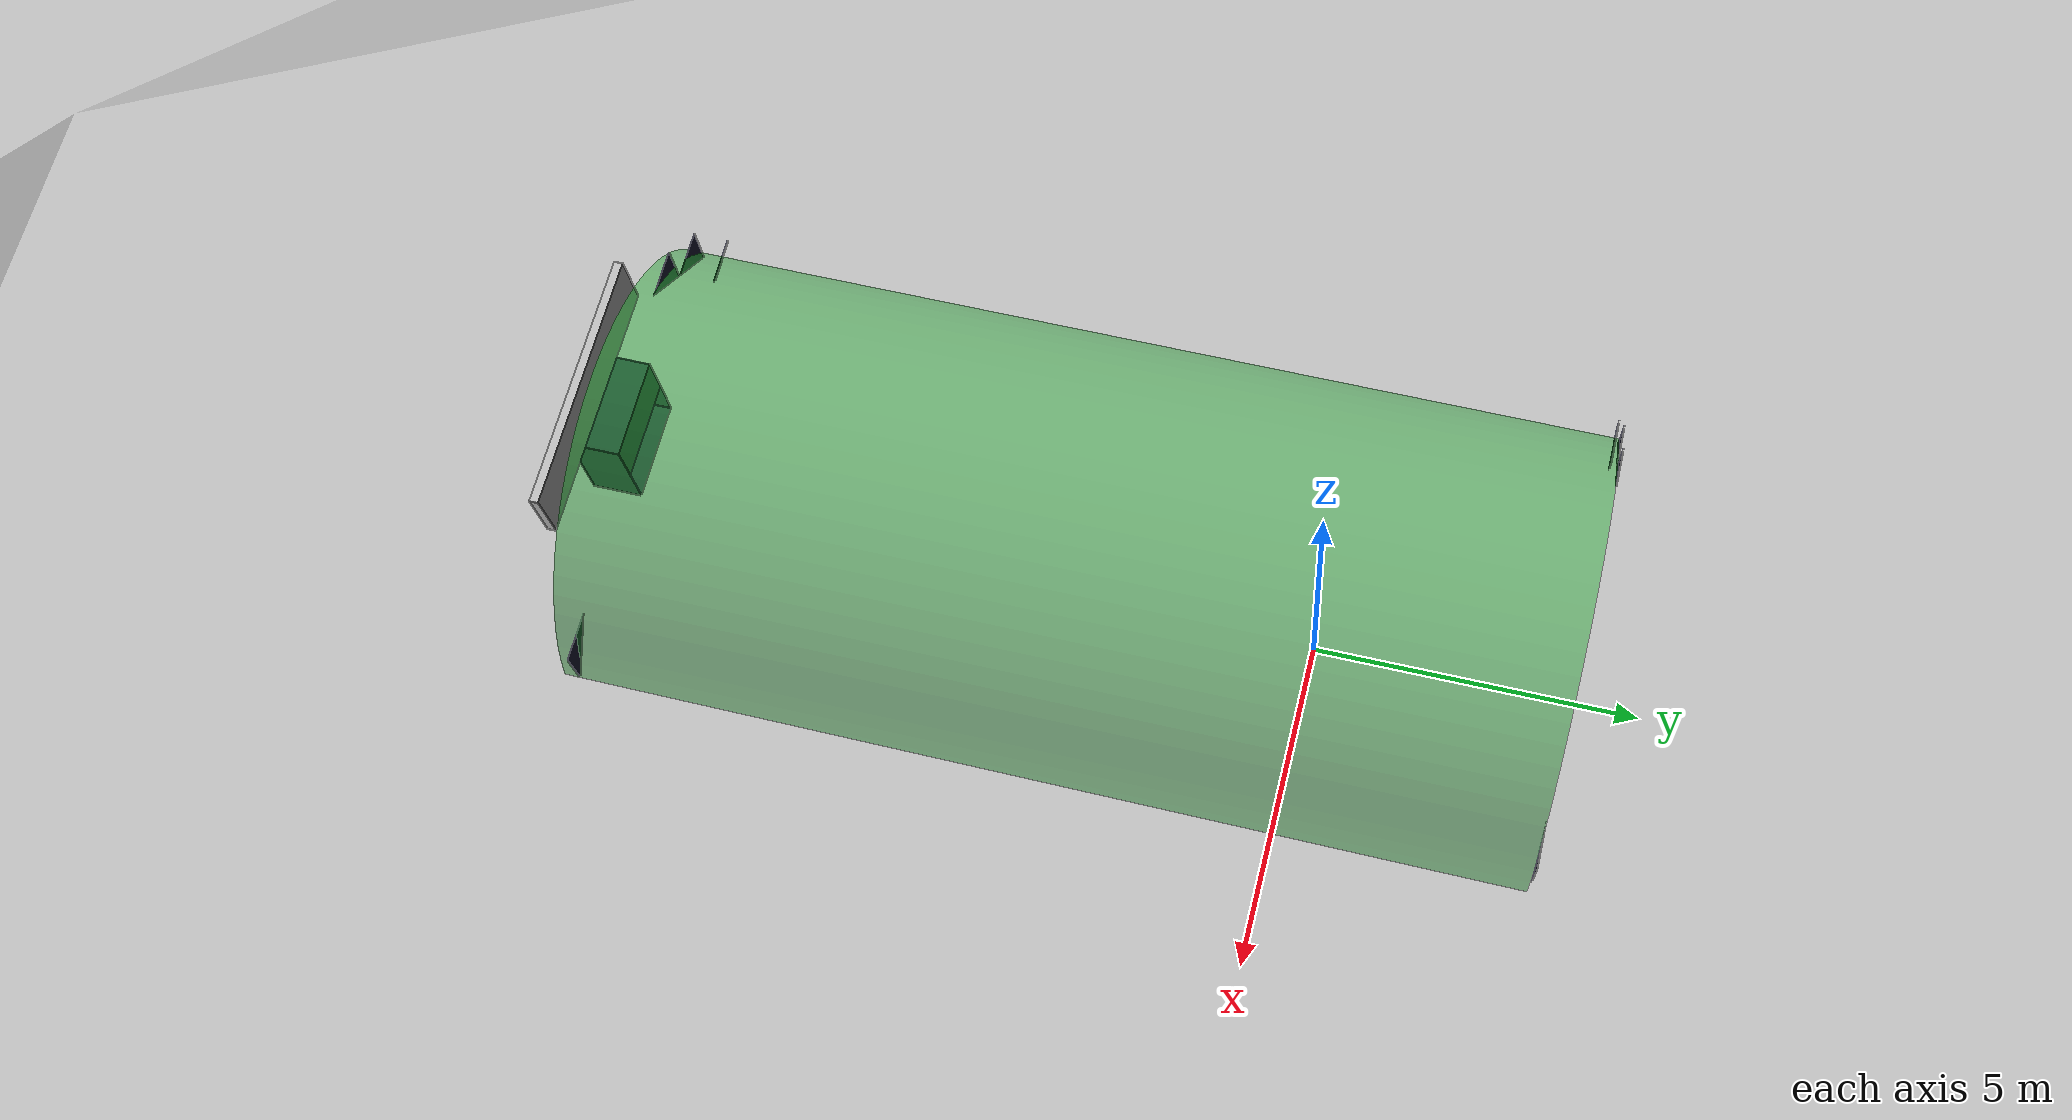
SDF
<sdf version="1.6">
 <world name="default">
  <light name="sun" type="directional">
   <pose>0 0 10 0 -0 0</pose>
   <diffuse>0.8 0.8 0.8 1</diffuse>
   <specular>0.2 0.2 0.2 1</specular>
   <attenuation>
    <range>1000</range>
    <constant>0.9</constant>
    <linear>0.01</linear>
    <quadratic>0.001</quadratic>
   </attenuation>
   <direction>-0.5 0.1 -0.9</direction>
  </light>
  <light name="light0" type="directional">
   <cast_shadows>0</cast_shadows>
   <pose>1.2 2.4 5 0 0 0</pose>
   <diffuse>0.8 0.8 0.8 1</diffuse>
   <specular>0.2 0.2 0.2 1</specular>
   <attenuation>
    <range>1000</range>
    <constant>0.9</constant>
    <linear>0.01</linear>
    <quadratic>0.001</quadratic>
   </attenuation>
   <direction>-0.5 0.1 -0.9</direction>
  </light>
  <light name="light1" type="directional">
   <cast_shadows>0</cast_shadows>
   <pose>0.297 -15.81 5 1.25 0 0</pose>
   <diffuse>0.8 0.8 0.8 1</diffuse>
   <specular>0.2 0.2 0.2 1</specular>
   <attenuation>
    <range>1000</range>
    <constant>0.9</constant>
    <linear>0.01</linear>
    <quadratic>0.001</quadratic>
   </attenuation>
   <direction>-0.5 0.1 -0.9</direction>
  </light>
  <light name="light2" type="directional">
   <cast_shadows>0</cast_shadows>
   <pose>4.63 30.098 9 -0.9 0 0</pose>
   <diffuse>0.8 0.8 0.8 1</diffuse>
   <specular>0.2 0.2 0.2 1</specular>
   <attenuation>
    <range>1000</range>
    <constant>0.9</constant>
    <linear>0.01</linear>
    <quadratic>0.001</quadratic>
   </attenuation>
   <direction>-0.5 0.1 -0.9</direction>
  </light>
  <scene><shadows>false</shadows><grid>false</grid><sky><clouds><speed>4</speed></clouds></sky></scene>
  <include><uri>model://farm1</uri><pose>1.424045 -8.25 0.15 -0.02 0.029 0</pose></include>
  <include><uri>model://green_house</uri><pose>10.32 -9.82 0.1 -1.57 -3.14 0</pose></include>
  <gravity>0 0 -9.8</gravity>
  <magnetic_field>6e-06 2.3e-05 -4.2e-05</magnetic_field>
  <atmosphere type="adiabatic"/>
  <physics name="default_physics" default="0" type="ode">
   <max_step_size>0.001</max_step_size>
   <real_time_factor>1</real_time_factor>
   <real_time_update_rate>1000</real_time_update_rate>
  </physics>
  <scene><ambient>0.4 0.4 0.4 1</ambient><background>0.7 0.7 0.7 1</background><shadows>1</shadows></scene>
  <spherical_coordinates>
   <surface_model>EARTH_WGS84</surface_model>
   <latitude_deg>0</latitude_deg>
   <longitude_deg>0</longitude_deg>
   <elevation>0</elevation>
   <heading_deg>0</heading_deg>
  </spherical_coordinates>
  <model name="plant00">
   <static>1</static>
   <link name="plant_3_link">
    <visual name="visual">
     <pose>0 0 -0.45 0 0 -1.57</pose>
     <geometry>
      <mesh><uri>model://plant/meshes/plant.obj</uri><scale>1.13768 1.13768 1.13768</scale></mesh>
     </geometry>
    </visual>
   </link>
   <link name="trough::trough_link">
    <visual name="visual"><geometry><mesh><uri>model://trough/meshes/truf.obj</uri></mesh></geometry></visual>
    <collision name="collision">
     <geometry><mesh><uri>model://trough/meshes/truf.obj</uri></mesh></geometry>
    </collision>
    <pose>0 0 0 1.57 -0 0</pose>
   </link>
   <link name="tomato_30::tomato_link">
    <visual name="visual"><geometry><mesh><uri>model://tomato/meshes/tomato.obj</uri></mesh></geometry></visual>
    <collision name="collision">
     <geometry><mesh><uri>model://tomato/meshes/tomato.obj</uri></mesh></geometry>
    </collision>
    <pose>-0.364 0.298 0.921 0 -0 0</pose>
   </link>
   <link name="tomato_31::tomato_link">
    <visual name="visual"><geometry><mesh><uri>model://tomato/meshes/tomato.obj</uri></mesh></geometry></visual>
    <collision name="collision">
     <geometry><mesh><uri>model://tomato/meshes/tomato.obj</uri></mesh></geometry>
    </collision>
    <pose>0.161 0.29 0.769 0 -0 0</pose>
   </link>
   <link name="tomato_32::tomato_link">
    <visual name="visual"><geometry><mesh><uri>model://tomato/meshes/tomato.obj</uri></mesh></geometry></visual>
    <collision name="collision">
     <geometry><mesh><uri>model://tomato/meshes/tomato.obj</uri></mesh></geometry>
    </collision>
    <pose>0.355 -0.152 1.751 0 -0 0</pose>
   </link>
   <link name="tomato_33::tomato_link">
    <visual name="visual"><geometry><mesh><uri>model://tomato/meshes/tomato.obj</uri></mesh></geometry></visual>
    <collision name="collision">
     <geometry><mesh><uri>model://tomato/meshes/tomato.obj</uri></mesh></geometry>
    </collision>
    <pose>0.036 -0.33 1.477 0 -0 0</pose>
   </link>
   <link name="tomato_34::tomato_link">
    <visual name="visual"><geometry><mesh><uri>model://tomato/meshes/tomato.obj</uri></mesh></geometry></visual>
    <collision name="collision">
     <geometry><mesh><uri>model://tomato/meshes/tomato.obj</uri></mesh></geometry>
    </collision>
    <pose>-0.294 -0.293 0.701 0 -0 0</pose>
   </link>
   <link name="tomato_35::tomato_link">
    <visual name="visual"><geometry><mesh><uri>model://tomato/meshes/tomato.obj</uri></mesh></geometry></visual>
    <collision name="collision">
     <geometry><mesh><uri>model://tomato/meshes/tomato.obj</uri></mesh></geometry>
    </collision>
    <pose>-0.388 0.032 1.317 0 -0 0</pose>
   </link>
   <link name="tomato_36::tomato_link">
    <visual name="visual"><geometry><mesh><uri>model://tomato/meshes/tomato.obj</uri></mesh></geometry></visual>
    <collision name="collision">
     <geometry><mesh><uri>model://tomato/meshes/tomato.obj</uri></mesh></geometry>
    </collision>
    <pose>0.374 0.157 1.317 0 -0 0</pose>
   </link>
   <link name="tomato_37::tomato_link">
    <visual name="visual"><geometry><mesh><uri>model://tomato/meshes/tomato.obj</uri></mesh></geometry></visual>
    <collision name="collision">
     <geometry><mesh><uri>model://tomato/meshes/tomato.obj</uri></mesh></geometry>
    </collision>
    <pose>0.036 -0.33 1.82 0 -0 0</pose>
   </link>
   <link name="tomato_38::tomato_link">
    <visual name="visual"><geometry><mesh><uri>model://tomato/meshes/tomato.obj</uri></mesh></geometry></visual>
    <collision name="collision">
     <geometry><mesh><uri>model://tomato/meshes/tomato.obj</uri></mesh></geometry>
    </collision>
    <pose>-0.102 -0.293 2.016 0 -0 0</pose>
   </link>
   <link name="tomato_39::tomato_link">
    <visual name="visual"><geometry><mesh><uri>model://tomato/meshes/tomato.obj</uri></mesh></geometry></visual>
    <collision name="collision">
     <geometry><mesh><uri>model://tomato/meshes/tomato.obj</uri></mesh></geometry>
    </collision>
    <pose>-0.388 0.032 1.82 0 -0 0</pose>
   </link>
   <pose>0 0 0 0 -0 1.57</pose>
  </model>
  <model name="plant01">
   <static>1</static>
   <link name="plant_2::plant">
    <visual name="visual"><geometry><mesh><uri>model://plant/meshes/plant.obj</uri></mesh></geometry></visual>
    <collision name="collision"><geometry><box><size>0.1 0.1 0.1</size></box></geometry></collision>
    <pose>0 0 -0.45 0 -0 0.338594</pose>
   </link>
   <link name="trough::trough_link">
    <visual name="visual"><geometry><mesh><uri>model://trough/meshes/truf.obj</uri></mesh></geometry></visual>
    <collision name="collision">
     <geometry><mesh><uri>model://trough/meshes/truf.obj</uri></mesh></geometry>
    </collision>
    <pose>0 0 0 1.57 -0 0</pose>
   </link>
   <link name="tomato_20::tomato_link">
    <visual name="visual"><geometry><mesh><uri>model://tomato/meshes/tomato.obj</uri></mesh></geometry></visual>
    <collision name="collision">
     <geometry><mesh><uri>model://tomato/meshes/tomato.obj</uri></mesh></geometry>
    </collision>
    <pose>-0.297 0.244 0.695 0 -0 0</pose>
   </link>
   <link name="tomato_21::tomato_link">
    <visual name="visual"><geometry><mesh><uri>model://tomato/meshes/tomato.obj</uri></mesh></geometry></visual>
    <collision name="collision">
     <geometry><mesh><uri>model://tomato/meshes/tomato.obj</uri></mesh></geometry>
    </collision>
    <pose>0.164 0.199 1.684 0 -0 0</pose>
   </link>
   <link name="tomato_22::tomato_link">
    <visual name="visual"><geometry><mesh><uri>model://tomato/meshes/tomato.obj</uri></mesh></geometry></visual>
    <collision name="collision">
     <geometry><mesh><uri>model://tomato/meshes/tomato.obj</uri></mesh></geometry>
    </collision>
    <pose>0.394 -0.151 0.705 0 -0 0</pose>
   </link>
   <link name="tomato_23::tomato_link">
    <visual name="visual"><geometry><mesh><uri>model://tomato/meshes/tomato.obj</uri></mesh></geometry></visual>
    <collision name="collision">
     <geometry><mesh><uri>model://tomato/meshes/tomato.obj</uri></mesh></geometry>
    </collision>
    <pose>0.054 -0.308 1.158 0 -0 0</pose>
   </link>
   <link name="tomato_24::tomato_link">
    <visual name="visual"><geometry><mesh><uri>model://tomato/meshes/tomato.obj</uri></mesh></geometry></visual>
    <collision name="collision">
     <geometry><mesh><uri>model://tomato/meshes/tomato.obj</uri></mesh></geometry>
    </collision>
    <pose>-0.236 -0.275 0.883 0 -0 0</pose>
   </link>
   <link name="tomato_25::tomato_link">
    <visual name="visual"><geometry><mesh><uri>model://tomato/meshes/tomato.obj</uri></mesh></geometry></visual>
    <collision name="collision">
     <geometry><mesh><uri>model://tomato/meshes/tomato.obj</uri></mesh></geometry>
    </collision>
    <pose>-0.318 0.01 1.158 0 -0 0</pose>
   </link>
   <link name="tomato_26::tomato_link">
    <visual name="visual"><geometry><mesh><uri>model://tomato/meshes/tomato.obj</uri></mesh></geometry></visual>
    <collision name="collision">
     <geometry><mesh><uri>model://tomato/meshes/tomato.obj</uri></mesh></geometry>
    </collision>
    <pose>0.351 0.12 1.158 0 -0 0</pose>
   </link>
   <link name="tomato_27::tomato_link">
    <visual name="visual"><geometry><mesh><uri>model://tomato/meshes/tomato.obj</uri></mesh></geometry></visual>
    <collision name="collision">
     <geometry><mesh><uri>model://tomato/meshes/tomato.obj</uri></mesh></geometry>
    </collision>
    <pose>0.054 -0.308 1.599 0 -0 0</pose>
   </link>
   <link name="tomato_28::tomato_link">
    <visual name="visual"><geometry><mesh><uri>model://tomato/meshes/tomato.obj</uri></mesh></geometry></visual>
    <collision name="collision">
     <geometry><mesh><uri>model://tomato/meshes/tomato.obj</uri></mesh></geometry>
    </collision>
    <pose>-0.236 -0.275 1.464 0 -0 0</pose>
   </link>
   <link name="tomato_29::tomato_link">
    <visual name="visual"><geometry><mesh><uri>model://tomato/meshes/tomato.obj</uri></mesh></geometry></visual>
    <collision name="collision">
     <geometry><mesh><uri>model://tomato/meshes/tomato.obj</uri></mesh></geometry>
    </collision>
    <pose>-0.318 0.01 1.599 0 -0 0</pose>
   </link>
   <pose>0 0.9 -0 0 -0 1.57</pose>
  </model>
  <model name="plant02">
   <static>1</static>
   <link name="plant_4::plant">
    <visual name="visual"><geometry><mesh><uri>model://plant/meshes/plant.obj</uri></mesh></geometry></visual>
    <collision name="collision"><geometry><box><size>0.1 0.1 0.1</size></box></geometry></collision>
    <pose>0 0 -0.45 0 0 -0.277507</pose>
   </link>
   <link name="trough::trough_link">
    <visual name="visual"><geometry><mesh><uri>model://trough/meshes/truf.obj</uri></mesh></geometry></visual>
    <collision name="collision">
     <geometry><mesh><uri>model://trough/meshes/truf.obj</uri></mesh></geometry>
    </collision>
    <pose>0 0 0 1.57 -0 0</pose>
   </link>
   <link name="tomato_40::tomato_link">
    <visual name="visual"><geometry><mesh><uri>model://tomato/meshes/tomato.obj</uri></mesh></geometry></visual>
    <collision name="collision">
     <geometry><mesh><uri>model://tomato/meshes/tomato.obj</uri></mesh></geometry>
    </collision>
    <pose>-0.297 0.244 0.669 0 -0 0</pose>
   </link>
   <link name="tomato_41::tomato_link">
    <visual name="visual"><geometry><mesh><uri>model://tomato/meshes/tomato.obj</uri></mesh></geometry></visual>
    <collision name="collision">
     <geometry><mesh><uri>model://tomato/meshes/tomato.obj</uri></mesh></geometry>
    </collision>
    <pose>0.073 0.375 1.175 0 -0 0</pose>
   </link>
   <link name="tomato_42::tomato_link">
    <visual name="visual"><geometry><mesh><uri>model://tomato/meshes/tomato.obj</uri></mesh></geometry></visual>
    <collision name="collision">
     <geometry><mesh><uri>model://tomato/meshes/tomato.obj</uri></mesh></geometry>
    </collision>
    <pose>0.196 -0.202 1.528 0 -0 0</pose>
   </link>
   <link name="tomato_43::tomato_link">
    <visual name="visual"><geometry><mesh><uri>model://tomato/meshes/tomato.obj</uri></mesh></geometry></visual>
    <collision name="collision">
     <geometry><mesh><uri>model://tomato/meshes/tomato.obj</uri></mesh></geometry>
    </collision>
    <pose>0.054 -0.237 0.732 0 -0 0</pose>
   </link>
   <link name="tomato_44::tomato_link">
    <visual name="visual"><geometry><mesh><uri>model://tomato/meshes/tomato.obj</uri></mesh></geometry></visual>
    <collision name="collision">
     <geometry><mesh><uri>model://tomato/meshes/tomato.obj</uri></mesh></geometry>
    </collision>
    <pose>-0.236 -0.275 0.851 0 -0 0</pose>
   </link>
   <link name="tomato_45::tomato_link">
    <visual name="visual"><geometry><mesh><uri>model://tomato/meshes/tomato.obj</uri></mesh></geometry></visual>
    <collision name="collision">
     <geometry><mesh><uri>model://tomato/meshes/tomato.obj</uri></mesh></geometry>
    </collision>
    <pose>-0.318 0.01 1.158 0 -0 0</pose>
   </link>
   <link name="tomato_46::tomato_link">
    <visual name="visual"><geometry><mesh><uri>model://tomato/meshes/tomato.obj</uri></mesh></geometry></visual>
    <collision name="collision">
     <geometry><mesh><uri>model://tomato/meshes/tomato.obj</uri></mesh></geometry>
    </collision>
    <pose>0.351 0.12 1.158 0 -0 0</pose>
   </link>
   <link name="tomato_47::tomato_link">
    <visual name="visual"><geometry><mesh><uri>model://tomato/meshes/tomato.obj</uri></mesh></geometry></visual>
    <collision name="collision">
     <geometry><mesh><uri>model://tomato/meshes/tomato.obj</uri></mesh></geometry>
    </collision>
    <pose>-0.039 -0.257 1.451 0 -0 0</pose>
   </link>
   <link name="tomato_48::tomato_link">
    <visual name="visual"><geometry><mesh><uri>model://tomato/meshes/tomato.obj</uri></mesh></geometry></visual>
    <collision name="collision">
     <geometry><mesh><uri>model://tomato/meshes/tomato.obj</uri></mesh></geometry>
    </collision>
    <pose>-0.236 -0.189 1.233 0 -0 0</pose>
   </link>
   <link name="tomato_49::tomato_link">
    <visual name="visual"><geometry><mesh><uri>model://tomato/meshes/tomato.obj</uri></mesh></geometry></visual>
    <collision name="collision">
     <geometry><mesh><uri>model://tomato/meshes/tomato.obj</uri></mesh></geometry>
    </collision>
    <pose>-0.318 0.01 1.599 0 -0 0</pose>
   </link>
   <pose>0 1.8 0 0 -0 1.57</pose>
  </model>
  <model name="plant03">
   <static>1</static>
   <link name="plant_2::plant">
    <visual name="visual"><geometry><mesh><uri>model://plant/meshes/plant.obj</uri></mesh></geometry></visual>
    <collision name="collision"><geometry><box><size>0.1 0.1 0.1</size></box></geometry></collision>
    <pose>0 0 -0.45 0 -0 0.338594</pose>
   </link>
   <link name="trough::trough_link">
    <visual name="visual"><geometry><mesh><uri>model://trough/meshes/truf.obj</uri></mesh></geometry></visual>
    <collision name="collision">
     <geometry><mesh><uri>model://trough/meshes/truf.obj</uri></mesh></geometry>
    </collision>
    <pose>0 0 0 1.57 -0 0</pose>
   </link>
   <link name="tomato_20::tomato_link">
    <visual name="visual"><geometry><mesh><uri>model://tomato/meshes/tomato.obj</uri></mesh></geometry></visual>
    <collision name="collision">
     <geometry><mesh><uri>model://tomato/meshes/tomato.obj</uri></mesh></geometry>
    </collision>
    <pose>-0.297 0.244 0.695 0 -0 0</pose>
   </link>
   <link name="tomato_21::tomato_link">
    <visual name="visual"><geometry><mesh><uri>model://tomato/meshes/tomato.obj</uri></mesh></geometry></visual>
    <collision name="collision">
     <geometry><mesh><uri>model://tomato/meshes/tomato.obj</uri></mesh></geometry>
    </collision>
    <pose>0.164 0.199 1.684 0 -0 0</pose>
   </link>
   <link name="tomato_22::tomato_link">
    <visual name="visual"><geometry><mesh><uri>model://tomato/meshes/tomato.obj</uri></mesh></geometry></visual>
    <collision name="collision">
     <geometry><mesh><uri>model://tomato/meshes/tomato.obj</uri></mesh></geometry>
    </collision>
    <pose>0.394 -0.151 0.705 0 -0 0</pose>
   </link>
   <link name="tomato_23::tomato_link">
    <visual name="visual"><geometry><mesh><uri>model://tomato/meshes/tomato.obj</uri></mesh></geometry></visual>
    <collision name="collision">
     <geometry><mesh><uri>model://tomato/meshes/tomato.obj</uri></mesh></geometry>
    </collision>
    <pose>0.054 -0.308 1.158 0 -0 0</pose>
   </link>
   <link name="tomato_24::tomato_link">
    <visual name="visual"><geometry><mesh><uri>model://tomato/meshes/tomato.obj</uri></mesh></geometry></visual>
    <collision name="collision">
     <geometry><mesh><uri>model://tomato/meshes/tomato.obj</uri></mesh></geometry>
    </collision>
    <pose>-0.236 -0.275 0.883 0 -0 0</pose>
   </link>
   <link name="tomato_25::tomato_link">
    <visual name="visual"><geometry><mesh><uri>model://tomato/meshes/tomato.obj</uri></mesh></geometry></visual>
    <collision name="collision">
     <geometry><mesh><uri>model://tomato/meshes/tomato.obj</uri></mesh></geometry>
    </collision>
    <pose>-0.318 0.01 1.158 0 -0 0</pose>
   </link>
   <link name="tomato_26::tomato_link">
    <visual name="visual"><geometry><mesh><uri>model://tomato/meshes/tomato.obj</uri></mesh></geometry></visual>
    <collision name="collision">
     <geometry><mesh><uri>model://tomato/meshes/tomato.obj</uri></mesh></geometry>
    </collision>
    <pose>0.351 0.12 1.158 0 -0 0</pose>
   </link>
   <link name="tomato_27::tomato_link">
    <visual name="visual"><geometry><mesh><uri>model://tomato/meshes/tomato.obj</uri></mesh></geometry></visual>
    <collision name="collision">
     <geometry><mesh><uri>model://tomato/meshes/tomato.obj</uri></mesh></geometry>
    </collision>
    <pose>0.054 -0.308 1.599 0 -0 0</pose>
   </link>
   <link name="tomato_28::tomato_link">
    <visual name="visual"><geometry><mesh><uri>model://tomato/meshes/tomato.obj</uri></mesh></geometry></visual>
    <collision name="collision">
     <geometry><mesh><uri>model://tomato/meshes/tomato.obj</uri></mesh></geometry>
    </collision>
    <pose>-0.236 -0.275 1.464 0 -0 0</pose>
   </link>
   <link name="tomato_29::tomato_link">
    <visual name="visual"><geometry><mesh><uri>model://tomato/meshes/tomato.obj</uri></mesh></geometry></visual>
    <collision name="collision">
     <geometry><mesh><uri>model://tomato/meshes/tomato.obj</uri></mesh></geometry>
    </collision>
    <pose>-0.318 0.01 1.599 0 -0 0</pose>
   </link>
   <pose>0 2.7 -0 0 -0 1.57</pose>
  </model>
  <model name="plant04">
   <static>1</static>
   <link name="plant_4::plant">
    <visual name="visual"><geometry><mesh><uri>model://plant/meshes/plant.obj</uri></mesh></geometry></visual>
    <collision name="collision"><geometry><box><size>0.1 0.1 0.1</size></box></geometry></collision>
    <pose>0 0 -0.45 0 0 -0.277507</pose>
   </link>
   <link name="trough::trough_link">
    <visual name="visual"><geometry><mesh><uri>model://trough/meshes/truf.obj</uri></mesh></geometry></visual>
    <collision name="collision">
     <geometry><mesh><uri>model://trough/meshes/truf.obj</uri></mesh></geometry>
    </collision>
    <pose>0 0 0 1.57 -0 0</pose>
   </link>
   <link name="tomato_40::tomato_link">
    <visual name="visual"><geometry><mesh><uri>model://tomato/meshes/tomato.obj</uri></mesh></geometry></visual>
    <collision name="collision">
     <geometry><mesh><uri>model://tomato/meshes/tomato.obj</uri></mesh></geometry>
    </collision>
    <pose>-0.297 0.244 0.669 0 -0 0</pose>
   </link>
   <link name="tomato_41::tomato_link">
    <visual name="visual"><geometry><mesh><uri>model://tomato/meshes/tomato.obj</uri></mesh></geometry></visual>
    <collision name="collision">
     <geometry><mesh><uri>model://tomato/meshes/tomato.obj</uri></mesh></geometry>
    </collision>
    <pose>0.073 0.375 1.175 0 -0 0</pose>
   </link>
   <link name="tomato_42::tomato_link">
    <visual name="visual"><geometry><mesh><uri>model://tomato/meshes/tomato.obj</uri></mesh></geometry></visual>
    <collision name="collision">
     <geometry><mesh><uri>model://tomato/meshes/tomato.obj</uri></mesh></geometry>
    </collision>
    <pose>0.196 -0.202 1.528 0 -0 0</pose>
   </link>
   <link name="tomato_43::tomato_link">
    <visual name="visual"><geometry><mesh><uri>model://tomato/meshes/tomato.obj</uri></mesh></geometry></visual>
    <collision name="collision">
     <geometry><mesh><uri>model://tomato/meshes/tomato.obj</uri></mesh></geometry>
    </collision>
    <pose>0.054 -0.237 0.732 0 -0 0</pose>
   </link>
   <link name="tomato_44::tomato_link">
    <visual name="visual"><geometry><mesh><uri>model://tomato/meshes/tomato.obj</uri></mesh></geometry></visual>
    <collision name="collision">
     <geometry><mesh><uri>model://tomato/meshes/tomato.obj</uri></mesh></geometry>
    </collision>
    <pose>-0.236 -0.275 0.851 0 -0 0</pose>
   </link>
   <link name="tomato_45::tomato_link">
    <visual name="visual"><geometry><mesh><uri>model://tomato/meshes/tomato.obj</uri></mesh></geometry></visual>
    <collision name="collision">
     <geometry><mesh><uri>model://tomato/meshes/tomato.obj</uri></mesh></geometry>
    </collision>
    <pose>-0.318 0.01 1.158 0 -0 0</pose>
   </link>
   <link name="tomato_46::tomato_link">
    <visual name="visual"><geometry><mesh><uri>model://tomato/meshes/tomato.obj</uri></mesh></geometry></visual>
    <collision name="collision">
     <geometry><mesh><uri>model://tomato/meshes/tomato.obj</uri></mesh></geometry>
    </collision>
    <pose>0.351 0.12 1.158 0 -0 0</pose>
   </link>
   <link name="tomato_47::tomato_link">
    <visual name="visual"><geometry><mesh><uri>model://tomato/meshes/tomato.obj</uri></mesh></geometry></visual>
    <collision name="collision">
     <geometry><mesh><uri>model://tomato/meshes/tomato.obj</uri></mesh></geometry>
    </collision>
    <pose>-0.039 -0.257 1.451 0 -0 0</pose>
   </link>
   <link name="tomato_48::tomato_link">
    <visual name="visual"><geometry><mesh><uri>model://tomato/meshes/tomato.obj</uri></mesh></geometry></visual>
    <collision name="collision">
     <geometry><mesh><uri>model://tomato/meshes/tomato.obj</uri></mesh></geometry>
    </collision>
    <pose>-0.236 -0.189 1.233 0 -0 0</pose>
   </link>
   <link name="tomato_49::tomato_link">
    <visual name="visual"><geometry><mesh><uri>model://tomato/meshes/tomato.obj</uri></mesh></geometry></visual>
    <collision name="collision">
     <geometry><mesh><uri>model://tomato/meshes/tomato.obj</uri></mesh></geometry>
    </collision>
    <pose>-0.318 0.01 1.599 0 -0 0</pose>
   </link>
   <pose>0 3.6 0 0 -0 1.57</pose>
  </model>
  <model name="plant05">
   <static>1</static>
   <link name="plant_1_link">
    <visual name="visual">
     <pose>0 0 -0.45 0 -0 0</pose>
     <geometry>
      <mesh><uri>model://plant/meshes/plant.obj</uri><scale>1.10961 1.10961 1.10961</scale></mesh>
     </geometry>
    </visual>
    <collision name="collision"><geometry><box><size>0.1 0.1 0.1</size></box></geometry></collision>
   </link>
   <link name="trough_1::trough_link">
    <visual name="visual"><geometry><mesh><uri>model://trough/meshes/truf.obj</uri></mesh></geometry></visual>
    <collision name="collision">
     <geometry><mesh><uri>model://trough/meshes/truf.obj</uri></mesh></geometry>
    </collision>
    <pose>0 0 0 1.57 -0 0</pose>
   </link>
   <link name="tomato_10::tomato_link">
    <visual name="visual"><geometry><mesh><uri>model://tomato/meshes/tomato.obj</uri></mesh></geometry></visual>
    <collision name="collision">
     <geometry><mesh><uri>model://tomato/meshes/tomato.obj</uri></mesh></geometry>
    </collision>
    <pose>-0.201 0.268 0.917 0 -0 0</pose>
   </link>
   <link name="tomato_11::tomato_link">
    <visual name="visual"><geometry><mesh><uri>model://tomato/meshes/tomato.obj</uri></mesh></geometry></visual>
    <collision name="collision">
     <geometry><mesh><uri>model://tomato/meshes/tomato.obj</uri></mesh></geometry>
    </collision>
    <pose>0.181 0.231 1.714 0 -0 0</pose>
   </link>
   <link name="tomato_12::tomato_link">
    <visual name="visual"><geometry><mesh><uri>model://tomato/meshes/tomato.obj</uri></mesh></geometry></visual>
    <collision name="collision">
     <geometry><mesh><uri>model://tomato/meshes/tomato.obj</uri></mesh></geometry>
    </collision>
    <pose>0.371 -0.171 1.608 0 -0 0</pose>
   </link>
   <link name="tomato_13::tomato_link">
    <visual name="visual"><geometry><mesh><uri>model://tomato/meshes/tomato.obj</uri></mesh></geometry></visual>
    <collision name="collision">
     <geometry><mesh><uri>model://tomato/meshes/tomato.obj</uri></mesh></geometry>
    </collision>
    <pose>0.059 -0.345 0.978 0 -0 0</pose>
   </link>
   <link name="tomato_14::tomato_link">
    <visual name="visual"><geometry><mesh><uri>model://tomato/meshes/tomato.obj</uri></mesh></geometry></visual>
    <collision name="collision">
     <geometry><mesh><uri>model://tomato/meshes/tomato.obj</uri></mesh></geometry>
    </collision>
    <pose>-0.263 -0.309 1.283 0 -0 0</pose>
   </link>
   <link name="tomato_15::tomato_link">
    <visual name="visual"><geometry><mesh><uri>model://tomato/meshes/tomato.obj</uri></mesh></geometry></visual>
    <collision name="collision">
     <geometry><mesh><uri>model://tomato/meshes/tomato.obj</uri></mesh></geometry>
    </collision>
    <pose>-0.354 0.008 1.283 0 -0 0</pose>
   </link>
   <link name="tomato_16::tomato_link">
    <visual name="visual"><geometry><mesh><uri>model://tomato/meshes/tomato.obj</uri></mesh></geometry></visual>
    <collision name="collision">
     <geometry><mesh><uri>model://tomato/meshes/tomato.obj</uri></mesh></geometry>
    </collision>
    <pose>0.389 0.13 1.096 0 -0 0</pose>
   </link>
   <link name="tomato_17::tomato_link">
    <visual name="visual"><geometry><mesh><uri>model://tomato/meshes/tomato.obj</uri></mesh></geometry></visual>
    <collision name="collision">
     <geometry><mesh><uri>model://tomato/meshes/tomato.obj</uri></mesh></geometry>
    </collision>
    <pose>0.059 -0.345 1.95 0 -0 0</pose>
   </link>
   <link name="tomato_18::tomato_link">
    <visual name="visual"><geometry><mesh><uri>model://tomato/meshes/tomato.obj</uri></mesh></geometry></visual>
    <collision name="collision">
     <geometry><mesh><uri>model://tomato/meshes/tomato.obj</uri></mesh></geometry>
    </collision>
    <pose>-0.263 -0.309 1.773 0 -0 0</pose>
   </link>
   <link name="tomato_19::tomato_link">
    <visual name="visual"><geometry><mesh><uri>model://tomato/meshes/tomato.obj</uri></mesh></geometry></visual>
    <collision name="collision">
     <geometry><mesh><uri>model://tomato/meshes/tomato.obj</uri></mesh></geometry>
    </collision>
    <pose>-0.354 0.008 1.773 0 -0 0</pose>
   </link>
   <pose>0 4.5 0 0 -0 1.57</pose>
  </model>
  <model name="plant06">
   <static>1</static>
   <link name="plant_3_link">
    <visual name="visual">
     <pose>0 0 -0.45 0 0 -1.57</pose>
     <geometry>
      <mesh><uri>model://plant/meshes/plant.obj</uri><scale>1.13768 1.13768 1.13768</scale></mesh>
     </geometry>
    </visual>
   </link>
   <link name="trough::trough_link">
    <visual name="visual"><geometry><mesh><uri>model://trough/meshes/truf.obj</uri></mesh></geometry></visual>
    <collision name="collision">
     <geometry><mesh><uri>model://trough/meshes/truf.obj</uri></mesh></geometry>
    </collision>
    <pose>0 0 0 1.57 -0 0</pose>
   </link>
   <link name="tomato_30::tomato_link">
    <visual name="visual"><geometry><mesh><uri>model://tomato/meshes/tomato.obj</uri></mesh></geometry></visual>
    <collision name="collision">
     <geometry><mesh><uri>model://tomato/meshes/tomato.obj</uri></mesh></geometry>
    </collision>
    <pose>-0.364 0.298 0.921 0 -0 0</pose>
   </link>
   <link name="tomato_31::tomato_link">
    <visual name="visual"><geometry><mesh><uri>model://tomato/meshes/tomato.obj</uri></mesh></geometry></visual>
    <collision name="collision">
     <geometry><mesh><uri>model://tomato/meshes/tomato.obj</uri></mesh></geometry>
    </collision>
    <pose>0.161 0.29 0.769 0 -0 0</pose>
   </link>
   <link name="tomato_32::tomato_link">
    <visual name="visual"><geometry><mesh><uri>model://tomato/meshes/tomato.obj</uri></mesh></geometry></visual>
    <collision name="collision">
     <geometry><mesh><uri>model://tomato/meshes/tomato.obj</uri></mesh></geometry>
    </collision>
    <pose>0.355 -0.152 1.751 0 -0 0</pose>
   </link>
   <link name="tomato_33::tomato_link">
    <visual name="visual"><geometry><mesh><uri>model://tomato/meshes/tomato.obj</uri></mesh></geometry></visual>
    <collision name="collision">
     <geometry><mesh><uri>model://tomato/meshes/tomato.obj</uri></mesh></geometry>
    </collision>
    <pose>0.036 -0.33 1.477 0 -0 0</pose>
   </link>
   <link name="tomato_34::tomato_link">
    <visual name="visual"><geometry><mesh><uri>model://tomato/meshes/tomato.obj</uri></mesh></geometry></visual>
    <collision name="collision">
     <geometry><mesh><uri>model://tomato/meshes/tomato.obj</uri></mesh></geometry>
    </collision>
    <pose>-0.294 -0.293 0.701 0 -0 0</pose>
   </link>
   <link name="tomato_35::tomato_link">
    <visual name="visual"><geometry><mesh><uri>model://tomato/meshes/tomato.obj</uri></mesh></geometry></visual>
    <collision name="collision">
     <geometry><mesh><uri>model://tomato/meshes/tomato.obj</uri></mesh></geometry>
    </collision>
    <pose>-0.388 0.032 1.317 0 -0 0</pose>
   </link>
   <link name="tomato_36::tomato_link">
    <visual name="visual"><geometry><mesh><uri>model://tomato/meshes/tomato.obj</uri></mesh></geometry></visual>
    <collision name="collision">
     <geometry><mesh><uri>model://tomato/meshes/tomato.obj</uri></mesh></geometry>
    </collision>
    <pose>0.374 0.157 1.317 0 -0 0</pose>
   </link>
   <link name="tomato_37::tomato_link">
    <visual name="visual"><geometry><mesh><uri>model://tomato/meshes/tomato.obj</uri></mesh></geometry></visual>
    <collision name="collision">
     <geometry><mesh><uri>model://tomato/meshes/tomato.obj</uri></mesh></geometry>
    </collision>
    <pose>0.036 -0.33 1.82 0 -0 0</pose>
   </link>
   <link name="tomato_38::tomato_link">
    <visual name="visual"><geometry><mesh><uri>model://tomato/meshes/tomato.obj</uri></mesh></geometry></visual>
    <collision name="collision">
     <geometry><mesh><uri>model://tomato/meshes/tomato.obj</uri></mesh></geometry>
    </collision>
    <pose>-0.102 -0.293 2.016 0 -0 0</pose>
   </link>
   <link name="tomato_39::tomato_link">
    <visual name="visual"><geometry><mesh><uri>model://tomato/meshes/tomato.obj</uri></mesh></geometry></visual>
    <collision name="collision">
     <geometry><mesh><uri>model://tomato/meshes/tomato.obj</uri></mesh></geometry>
    </collision>
    <pose>-0.388 0.032 1.82 0 -0 0</pose>
   </link>
   <pose>0 5.4 0 0 -0 1.57</pose>
  </model>
  <model name="plant07">
   <static>1</static>
   <link name="plant_1_link">
    <visual name="visual">
     <pose>0 0 -0.45 0 -0 0</pose>
     <geometry>
      <mesh><uri>model://plant/meshes/plant.obj</uri><scale>1.10961 1.10961 1.10961</scale></mesh>
     </geometry>
    </visual>
    <collision name="collision"><geometry><box><size>0.1 0.1 0.1</size></box></geometry></collision>
   </link>
   <link name="trough_1::trough_link">
    <visual name="visual"><geometry><mesh><uri>model://trough/meshes/truf.obj</uri></mesh></geometry></visual>
    <collision name="collision">
     <geometry><mesh><uri>model://trough/meshes/truf.obj</uri></mesh></geometry>
    </collision>
    <pose>0 0 0 1.57 -0 0</pose>
   </link>
   <link name="tomato_10::tomato_link">
    <visual name="visual"><geometry><mesh><uri>model://tomato/meshes/tomato.obj</uri></mesh></geometry></visual>
    <collision name="collision">
     <geometry><mesh><uri>model://tomato/meshes/tomato.obj</uri></mesh></geometry>
    </collision>
    <pose>-0.201 0.268 0.917 0 -0 0</pose>
   </link>
   <link name="tomato_11::tomato_link">
    <visual name="visual"><geometry><mesh><uri>model://tomato/meshes/tomato.obj</uri></mesh></geometry></visual>
    <collision name="collision">
     <geometry><mesh><uri>model://tomato/meshes/tomato.obj</uri></mesh></geometry>
    </collision>
    <pose>0.181 0.231 1.714 0 -0 0</pose>
   </link>
   <link name="tomato_12::tomato_link">
    <visual name="visual"><geometry><mesh><uri>model://tomato/meshes/tomato.obj</uri></mesh></geometry></visual>
    <collision name="collision">
     <geometry><mesh><uri>model://tomato/meshes/tomato.obj</uri></mesh></geometry>
    </collision>
    <pose>0.371 -0.171 1.608 0 -0 0</pose>
   </link>
   <link name="tomato_13::tomato_link">
    <visual name="visual"><geometry><mesh><uri>model://tomato/meshes/tomato.obj</uri></mesh></geometry></visual>
    <collision name="collision">
     <geometry><mesh><uri>model://tomato/meshes/tomato.obj</uri></mesh></geometry>
    </collision>
    <pose>0.059 -0.345 0.978 0 -0 0</pose>
   </link>
   <link name="tomato_14::tomato_link">
    <visual name="visual"><geometry><mesh><uri>model://tomato/meshes/tomato.obj</uri></mesh></geometry></visual>
    <collision name="collision">
     <geometry><mesh><uri>model://tomato/meshes/tomato.obj</uri></mesh></geometry>
    </collision>
    <pose>-0.263 -0.309 1.283 0 -0 0</pose>
   </link>
   <link name="tomato_15::tomato_link">
    <visual name="visual"><geometry><mesh><uri>model://tomato/meshes/tomato.obj</uri></mesh></geometry></visual>
    <collision name="collision">
     <geometry><mesh><uri>model://tomato/meshes/tomato.obj</uri></mesh></geometry>
    </collision>
    <pose>-0.354 0.008 1.283 0 -0 0</pose>
   </link>
   <link name="tomato_16::tomato_link">
    <visual name="visual"><geometry><mesh><uri>model://tomato/meshes/tomato.obj</uri></mesh></geometry></visual>
    <collision name="collision">
     <geometry><mesh><uri>model://tomato/meshes/tomato.obj</uri></mesh></geometry>
    </collision>
    <pose>0.389 0.13 1.096 0 -0 0</pose>
   </link>
   <link name="tomato_17::tomato_link">
    <visual name="visual"><geometry><mesh><uri>model://tomato/meshes/tomato.obj</uri></mesh></geometry></visual>
    <collision name="collision">
     <geometry><mesh><uri>model://tomato/meshes/tomato.obj</uri></mesh></geometry>
    </collision>
    <pose>0.059 -0.345 1.95 0 -0 0</pose>
   </link>
   <link name="tomato_18::tomato_link">
    <visual name="visual"><geometry><mesh><uri>model://tomato/meshes/tomato.obj</uri></mesh></geometry></visual>
    <collision name="collision">
     <geometry><mesh><uri>model://tomato/meshes/tomato.obj</uri></mesh></geometry>
    </collision>
    <pose>-0.263 -0.309 1.773 0 -0 0</pose>
   </link>
   <link name="tomato_19::tomato_link">
    <visual name="visual"><geometry><mesh><uri>model://tomato/meshes/tomato.obj</uri></mesh></geometry></visual>
    <collision name="collision">
     <geometry><mesh><uri>model://tomato/meshes/tomato.obj</uri></mesh></geometry>
    </collision>
    <pose>-0.354 0.008 1.773 0 -0 0</pose>
   </link>
   <pose>0 6.3 0 0 -0 1.57</pose>
  </model>
  <model name="plant08">
   <static>1</static>
   <link name="plant_4::plant">
    <visual name="visual"><geometry><mesh><uri>model://plant/meshes/plant.obj</uri></mesh></geometry></visual>
    <collision name="collision"><geometry><box><size>0.1 0.1 0.1</size></box></geometry></collision>
    <pose>0 0 -0.45 0 0 -0.277507</pose>
   </link>
   <link name="trough::trough_link">
    <visual name="visual"><geometry><mesh><uri>model://trough/meshes/truf.obj</uri></mesh></geometry></visual>
    <collision name="collision">
     <geometry><mesh><uri>model://trough/meshes/truf.obj</uri></mesh></geometry>
    </collision>
    <pose>0 0 0 1.57 -0 0</pose>
   </link>
   <link name="tomato_40::tomato_link">
    <visual name="visual"><geometry><mesh><uri>model://tomato/meshes/tomato.obj</uri></mesh></geometry></visual>
    <collision name="collision">
     <geometry><mesh><uri>model://tomato/meshes/tomato.obj</uri></mesh></geometry>
    </collision>
    <pose>-0.297 0.244 0.669 0 -0 0</pose>
   </link>
   <link name="tomato_41::tomato_link">
    <visual name="visual"><geometry><mesh><uri>model://tomato/meshes/tomato.obj</uri></mesh></geometry></visual>
    <collision name="collision">
     <geometry><mesh><uri>model://tomato/meshes/tomato.obj</uri></mesh></geometry>
    </collision>
    <pose>0.073 0.375 1.175 0 -0 0</pose>
   </link>
   <link name="tomato_42::tomato_link">
    <visual name="visual"><geometry><mesh><uri>model://tomato/meshes/tomato.obj</uri></mesh></geometry></visual>
    <collision name="collision">
     <geometry><mesh><uri>model://tomato/meshes/tomato.obj</uri></mesh></geometry>
    </collision>
    <pose>0.196 -0.202 1.528 0 -0 0</pose>
   </link>
   <link name="tomato_43::tomato_link">
    <visual name="visual"><geometry><mesh><uri>model://tomato/meshes/tomato.obj</uri></mesh></geometry></visual>
    <collision name="collision">
     <geometry><mesh><uri>model://tomato/meshes/tomato.obj</uri></mesh></geometry>
    </collision>
    <pose>0.054 -0.237 0.732 0 -0 0</pose>
   </link>
   <link name="tomato_44::tomato_link">
    <visual name="visual"><geometry><mesh><uri>model://tomato/meshes/tomato.obj</uri></mesh></geometry></visual>
    <collision name="collision">
     <geometry><mesh><uri>model://tomato/meshes/tomato.obj</uri></mesh></geometry>
    </collision>
    <pose>-0.236 -0.275 0.851 0 -0 0</pose>
   </link>
   <link name="tomato_45::tomato_link">
    <visual name="visual"><geometry><mesh><uri>model://tomato/meshes/tomato.obj</uri></mesh></geometry></visual>
    <collision name="collision">
     <geometry><mesh><uri>model://tomato/meshes/tomato.obj</uri></mesh></geometry>
    </collision>
    <pose>-0.318 0.01 1.158 0 -0 0</pose>
   </link>
   <link name="tomato_46::tomato_link">
    <visual name="visual"><geometry><mesh><uri>model://tomato/meshes/tomato.obj</uri></mesh></geometry></visual>
    <collision name="collision">
     <geometry><mesh><uri>model://tomato/meshes/tomato.obj</uri></mesh></geometry>
    </collision>
    <pose>0.351 0.12 1.158 0 -0 0</pose>
   </link>
   <link name="tomato_47::tomato_link">
    <visual name="visual"><geometry><mesh><uri>model://tomato/meshes/tomato.obj</uri></mesh></geometry></visual>
    <collision name="collision">
     <geometry><mesh><uri>model://tomato/meshes/tomato.obj</uri></mesh></geometry>
    </collision>
    <pose>-0.039 -0.257 1.451 0 -0 0</pose>
   </link>
   <link name="tomato_48::tomato_link">
    <visual name="visual"><geometry><mesh><uri>model://tomato/meshes/tomato.obj</uri></mesh></geometry></visual>
    <collision name="collision">
     <geometry><mesh><uri>model://tomato/meshes/tomato.obj</uri></mesh></geometry>
    </collision>
    <pose>-0.236 -0.189 1.233 0 -0 0</pose>
   </link>
   <link name="tomato_49::tomato_link">
    <visual name="visual"><geometry><mesh><uri>model://tomato/meshes/tomato.obj</uri></mesh></geometry></visual>
    <collision name="collision">
     <geometry><mesh><uri>model://tomato/meshes/tomato.obj</uri></mesh></geometry>
    </collision>
    <pose>-0.318 0.01 1.599 0 -0 0</pose>
   </link>
   <pose>0 7.2 0 0 -0 1.57</pose>
  </model>
  <model name="plant09">
   <static>1</static>
   <link name="plant_1_link">
    <visual name="visual">
     <pose>0 0 -0.45 0 -0 0</pose>
     <geometry>
      <mesh><uri>model://plant/meshes/plant.obj</uri><scale>1.10961 1.10961 1.10961</scale></mesh>
     </geometry>
    </visual>
    <collision name="collision"><geometry><box><size>0.1 0.1 0.1</size></box></geometry></collision>
   </link>
   <link name="trough_1::trough_link">
    <visual name="visual"><geometry><mesh><uri>model://trough/meshes/truf.obj</uri></mesh></geometry></visual>
    <collision name="collision">
     <geometry><mesh><uri>model://trough/meshes/truf.obj</uri></mesh></geometry>
    </collision>
    <pose>0 0 0 1.57 -0 0</pose>
   </link>
   <link name="tomato_10::tomato_link">
    <visual name="visual"><geometry><mesh><uri>model://tomato/meshes/tomato.obj</uri></mesh></geometry></visual>
    <collision name="collision">
     <geometry><mesh><uri>model://tomato/meshes/tomato.obj</uri></mesh></geometry>
    </collision>
    <pose>-0.201 0.268 0.917 0 -0 0</pose>
   </link>
   <link name="tomato_11::tomato_link">
    <visual name="visual"><geometry><mesh><uri>model://tomato/meshes/tomato.obj</uri></mesh></geometry></visual>
    <collision name="collision">
     <geometry><mesh><uri>model://tomato/meshes/tomato.obj</uri></mesh></geometry>
    </collision>
    <pose>0.181 0.231 1.714 0 -0 0</pose>
   </link>
   <link name="tomato_12::tomato_link">
    <visual name="visual"><geometry><mesh><uri>model://tomato/meshes/tomato.obj</uri></mesh></geometry></visual>
    <collision name="collision">
     <geometry><mesh><uri>model://tomato/meshes/tomato.obj</uri></mesh></geometry>
    </collision>
    <pose>0.371 -0.171 1.608 0 -0 0</pose>
   </link>
   <link name="tomato_13::tomato_link">
    <visual name="visual"><geometry><mesh><uri>model://tomato/meshes/tomato.obj</uri></mesh></geometry></visual>
    <collision name="collision">
     <geometry><mesh><uri>model://tomato/meshes/tomato.obj</uri></mesh></geometry>
    </collision>
    <pose>0.059 -0.345 0.978 0 -0 0</pose>
   </link>
   <link name="tomato_14::tomato_link">
    <visual name="visual"><geometry><mesh><uri>model://tomato/meshes/tomato.obj</uri></mesh></geometry></visual>
    <collision name="collision">
     <geometry><mesh><uri>model://tomato/meshes/tomato.obj</uri></mesh></geometry>
    </collision>
    <pose>-0.263 -0.309 1.283 0 -0 0</pose>
   </link>
   <link name="tomato_15::tomato_link">
    <visual name="visual"><geometry><mesh><uri>model://tomato/meshes/tomato.obj</uri></mesh></geometry></visual>
    <collision name="collision">
     <geometry><mesh><uri>model://tomato/meshes/tomato.obj</uri></mesh></geometry>
    </collision>
    <pose>-0.354 0.008 1.283 0 -0 0</pose>
   </link>
   <link name="tomato_16::tomato_link">
    <visual name="visual"><geometry><mesh><uri>model://tomato/meshes/tomato.obj</uri></mesh></geometry></visual>
    <collision name="collision">
     <geometry><mesh><uri>model://tomato/meshes/tomato.obj</uri></mesh></geometry>
    </collision>
    <pose>0.389 0.13 1.096 0 -0 0</pose>
   </link>
   <link name="tomato_17::tomato_link">
    <visual name="visual"><geometry><mesh><uri>model://tomato/meshes/tomato.obj</uri></mesh></geometry></visual>
    <collision name="collision">
     <geometry><mesh><uri>model://tomato/meshes/tomato.obj</uri></mesh></geometry>
    </collision>
    <pose>0.059 -0.345 1.95 0 -0 0</pose>
   </link>
   <link name="tomato_18::tomato_link">
    <visual name="visual"><geometry><mesh><uri>model://tomato/meshes/tomato.obj</uri></mesh></geometry></visual>
    <collision name="collision">
     <geometry><mesh><uri>model://tomato/meshes/tomato.obj</uri></mesh></geometry>
    </collision>
    <pose>-0.263 -0.309 1.773 0 -0 0</pose>
   </link>
   <link name="tomato_19::tomato_link">
    <visual name="visual"><geometry><mesh><uri>model://tomato/meshes/tomato.obj</uri></mesh></geometry></visual>
    <collision name="collision">
     <geometry><mesh><uri>model://tomato/meshes/tomato.obj</uri></mesh></geometry>
    </collision>
    <pose>-0.354 0.008 1.773 0 -0 0</pose>
   </link>
   <pose>0 8.1 0 0 -0 1.57</pose>
  </model>
  <model name="plant10">
   <static>1</static>
   <link name="plant_1_link">
    <visual name="visual">
     <pose>0 0 -0.45 0 -0 0</pose>
     <geometry>
      <mesh><uri>model://plant/meshes/plant.obj</uri><scale>1.10961 1.10961 1.10961</scale></mesh>
     </geometry>
    </visual>
    <collision name="collision"><geometry><box><size>0.1 0.1 0.1</size></box></geometry></collision>
   </link>
   <link name="trough_1::trough_link">
    <visual name="visual"><geometry><mesh><uri>model://trough/meshes/truf.obj</uri></mesh></geometry></visual>
    <collision name="collision">
     <geometry><mesh><uri>model://trough/meshes/truf.obj</uri></mesh></geometry>
    </collision>
    <pose>0 0 0 1.57 -0 0</pose>
   </link>
   <link name="tomato_10::tomato_link">
    <visual name="visual"><geometry><mesh><uri>model://tomato/meshes/tomato.obj</uri></mesh></geometry></visual>
    <collision name="collision">
     <geometry><mesh><uri>model://tomato/meshes/tomato.obj</uri></mesh></geometry>
    </collision>
    <pose>-0.201 0.268 0.917 0 -0 0</pose>
   </link>
   <link name="tomato_11::tomato_link">
    <visual name="visual"><geometry><mesh><uri>model://tomato/meshes/tomato.obj</uri></mesh></geometry></visual>
    <collision name="collision">
     <geometry><mesh><uri>model://tomato/meshes/tomato.obj</uri></mesh></geometry>
    </collision>
    <pose>0.181 0.231 1.714 0 -0 0</pose>
   </link>
   <link name="tomato_12::tomato_link">
    <visual name="visual"><geometry><mesh><uri>model://tomato/meshes/tomato.obj</uri></mesh></geometry></visual>
    <collision name="collision">
     <geometry><mesh><uri>model://tomato/meshes/tomato.obj</uri></mesh></geometry>
    </collision>
    <pose>0.371 -0.171 1.608 0 -0 0</pose>
   </link>
   <link name="tomato_13::tomato_link">
    <visual name="visual"><geometry><mesh><uri>model://tomato/meshes/tomato.obj</uri></mesh></geometry></visual>
    <collision name="collision">
     <geometry><mesh><uri>model://tomato/meshes/tomato.obj</uri></mesh></geometry>
    </collision>
    <pose>0.059 -0.345 0.978 0 -0 0</pose>
   </link>
   <link name="tomato_14::tomato_link">
    <visual name="visual"><geometry><mesh><uri>model://tomato/meshes/tomato.obj</uri></mesh></geometry></visual>
    <collision name="collision">
     <geometry><mesh><uri>model://tomato/meshes/tomato.obj</uri></mesh></geometry>
    </collision>
    <pose>-0.263 -0.309 1.283 0 -0 0</pose>
   </link>
   <link name="tomato_15::tomato_link">
    <visual name="visual"><geometry><mesh><uri>model://tomato/meshes/tomato.obj</uri></mesh></geometry></visual>
    <collision name="collision">
     <geometry><mesh><uri>model://tomato/meshes/tomato.obj</uri></mesh></geometry>
    </collision>
    <pose>-0.354 0.008 1.283 0 -0 0</pose>
   </link>
   <link name="tomato_16::tomato_link">
    <visual name="visual"><geometry><mesh><uri>model://tomato/meshes/tomato.obj</uri></mesh></geometry></visual>
    <collision name="collision">
     <geometry><mesh><uri>model://tomato/meshes/tomato.obj</uri></mesh></geometry>
    </collision>
    <pose>0.389 0.13 1.096 0 -0 0</pose>
   </link>
   <link name="tomato_17::tomato_link">
    <visual name="visual"><geometry><mesh><uri>model://tomato/meshes/tomato.obj</uri></mesh></geometry></visual>
    <collision name="collision">
     <geometry><mesh><uri>model://tomato/meshes/tomato.obj</uri></mesh></geometry>
    </collision>
    <pose>0.059 -0.345 1.95 0 -0 0</pose>
   </link>
   <link name="tomato_18::tomato_link">
    <visual name="visual"><geometry><mesh><uri>model://tomato/meshes/tomato.obj</uri></mesh></geometry></visual>
    <collision name="collision">
     <geometry><mesh><uri>model://tomato/meshes/tomato.obj</uri></mesh></geometry>
    </collision>
    <pose>-0.263 -0.309 1.773 0 -0 0</pose>
   </link>
   <link name="tomato_19::tomato_link">
    <visual name="visual"><geometry><mesh><uri>model://tomato/meshes/tomato.obj</uri></mesh></geometry></visual>
    <collision name="collision">
     <geometry><mesh><uri>model://tomato/meshes/tomato.obj</uri></mesh></geometry>
    </collision>
    <pose>-0.354 0.008 1.773 0 -0 0</pose>
   </link>
   <pose>2 0 0 0 -0 1.57</pose>
  </model>
  <model name="plant11">
   <static>1</static>
   <link name="plant_4::plant">
    <visual name="visual"><geometry><mesh><uri>model://plant/meshes/plant.obj</uri></mesh></geometry></visual>
    <collision name="collision"><geometry><box><size>0.1 0.1 0.1</size></box></geometry></collision>
    <pose>0 0 -0.45 0 0 -0.277507</pose>
   </link>
   <link name="trough::trough_link">
    <visual name="visual"><geometry><mesh><uri>model://trough/meshes/truf.obj</uri></mesh></geometry></visual>
    <collision name="collision">
     <geometry><mesh><uri>model://trough/meshes/truf.obj</uri></mesh></geometry>
    </collision>
    <pose>0 0 0 1.57 -0 0</pose>
   </link>
   <link name="tomato_40::tomato_link">
    <visual name="visual"><geometry><mesh><uri>model://tomato/meshes/tomato.obj</uri></mesh></geometry></visual>
    <collision name="collision">
     <geometry><mesh><uri>model://tomato/meshes/tomato.obj</uri></mesh></geometry>
    </collision>
    <pose>-0.297 0.244 0.669 0 -0 0</pose>
   </link>
   <link name="tomato_41::tomato_link">
    <visual name="visual"><geometry><mesh><uri>model://tomato/meshes/tomato.obj</uri></mesh></geometry></visual>
    <collision name="collision">
     <geometry><mesh><uri>model://tomato/meshes/tomato.obj</uri></mesh></geometry>
    </collision>
    <pose>0.073 0.375 1.175 0 -0 0</pose>
   </link>
   <link name="tomato_42::tomato_link">
    <visual name="visual"><geometry><mesh><uri>model://tomato/meshes/tomato.obj</uri></mesh></geometry></visual>
    <collision name="collision">
     <geometry><mesh><uri>model://tomato/meshes/tomato.obj</uri></mesh></geometry>
    </collision>
    <pose>0.196 -0.202 1.528 0 -0 0</pose>
   </link>
   <link name="tomato_43::tomato_link">
    <visual name="visual"><geometry><mesh><uri>model://tomato/meshes/tomato.obj</uri></mesh></geometry></visual>
    <collision name="collision">
     <geometry><mesh><uri>model://tomato/meshes/tomato.obj</uri></mesh></geometry>
    </collision>
    <pose>0.054 -0.237 0.732 0 -0 0</pose>
   </link>
   <link name="tomato_44::tomato_link">
    <visual name="visual"><geometry><mesh><uri>model://tomato/meshes/tomato.obj</uri></mesh></geometry></visual>
    <collision name="collision">
     <geometry><mesh><uri>model://tomato/meshes/tomato.obj</uri></mesh></geometry>
    </collision>
    <pose>-0.236 -0.275 0.851 0 -0 0</pose>
   </link>
   <link name="tomato_45::tomato_link">
    <visual name="visual"><geometry><mesh><uri>model://tomato/meshes/tomato.obj</uri></mesh></geometry></visual>
    <collision name="collision">
     <geometry><mesh><uri>model://tomato/meshes/tomato.obj</uri></mesh></geometry>
    </collision>
    <pose>-0.318 0.01 1.158 0 -0 0</pose>
   </link>
   <link name="tomato_46::tomato_link">
    <visual name="visual"><geometry><mesh><uri>model://tomato/meshes/tomato.obj</uri></mesh></geometry></visual>
    <collision name="collision">
     <geometry><mesh><uri>model://tomato/meshes/tomato.obj</uri></mesh></geometry>
    </collision>
    <pose>0.351 0.12 1.158 0 -0 0</pose>
   </link>
   <link name="tomato_47::tomato_link">
    <visual name="visual"><geometry><mesh><uri>model://tomato/meshes/tomato.obj</uri></mesh></geometry></visual>
    <collision name="collision">
     <geometry><mesh><uri>model://tomato/meshes/tomato.obj</uri></mesh></geometry>
    </collision>
    <pose>-0.039 -0.257 1.451 0 -0 0</pose>
   </link>
   <link name="tomato_48::tomato_link">
    <visual name="visual"><geometry><mesh><uri>model://tomato/meshes/tomato.obj</uri></mesh></geometry></visual>
    <collision name="collision">
     <geometry><mesh><uri>model://tomato/meshes/tomato.obj</uri></mesh></geometry>
    </collision>
    <pose>-0.236 -0.189 1.233 0 -0 0</pose>
   </link>
   <link name="tomato_49::tomato_link">
    <visual name="visual"><geometry><mesh><uri>model://tomato/meshes/tomato.obj</uri></mesh></geometry></visual>
    <collision name="collision">
     <geometry><mesh><uri>model://tomato/meshes/tomato.obj</uri></mesh></geometry>
    </collision>
    <pose>-0.318 0.01 1.599 0 -0 0</pose>
   </link>
   <pose>2 0.9 0 0 -0 1.57</pose>
  </model>
  <model name="plant12">
   <static>1</static>
   <link name="plant_4::plant">
    <visual name="visual"><geometry><mesh><uri>model://plant/meshes/plant.obj</uri></mesh></geometry></visual>
    <collision name="collision"><geometry><box><size>0.1 0.1 0.1</size></box></geometry></collision>
    <pose>0 0 -0.45 0 0 -0.277507</pose>
   </link>
   <link name="trough::trough_link">
    <visual name="visual"><geometry><mesh><uri>model://trough/meshes/truf.obj</uri></mesh></geometry></visual>
    <collision name="collision">
     <geometry><mesh><uri>model://trough/meshes/truf.obj</uri></mesh></geometry>
    </collision>
    <pose>0 0 0 1.57 -0 0</pose>
   </link>
   <link name="tomato_40::tomato_link">
    <visual name="visual"><geometry><mesh><uri>model://tomato/meshes/tomato.obj</uri></mesh></geometry></visual>
    <collision name="collision">
     <geometry><mesh><uri>model://tomato/meshes/tomato.obj</uri></mesh></geometry>
    </collision>
    <pose>-0.297 0.244 0.669 0 -0 0</pose>
   </link>
   <link name="tomato_41::tomato_link">
    <visual name="visual"><geometry><mesh><uri>model://tomato/meshes/tomato.obj</uri></mesh></geometry></visual>
    <collision name="collision">
     <geometry><mesh><uri>model://tomato/meshes/tomato.obj</uri></mesh></geometry>
    </collision>
    <pose>0.073 0.375 1.175 0 -0 0</pose>
   </link>
   <link name="tomato_42::tomato_link">
    <visual name="visual"><geometry><mesh><uri>model://tomato/meshes/tomato.obj</uri></mesh></geometry></visual>
    <collision name="collision">
     <geometry><mesh><uri>model://tomato/meshes/tomato.obj</uri></mesh></geometry>
    </collision>
    <pose>0.196 -0.202 1.528 0 -0 0</pose>
   </link>
   <link name="tomato_43::tomato_link">
    <visual name="visual"><geometry><mesh><uri>model://tomato/meshes/tomato.obj</uri></mesh></geometry></visual>
    <collision name="collision">
     <geometry><mesh><uri>model://tomato/meshes/tomato.obj</uri></mesh></geometry>
    </collision>
    <pose>0.054 -0.237 0.732 0 -0 0</pose>
   </link>
   <link name="tomato_44::tomato_link">
    <visual name="visual"><geometry><mesh><uri>model://tomato/meshes/tomato.obj</uri></mesh></geometry></visual>
    <collision name="collision">
     <geometry><mesh><uri>model://tomato/meshes/tomato.obj</uri></mesh></geometry>
    </collision>
    <pose>-0.236 -0.275 0.851 0 -0 0</pose>
   </link>
   <link name="tomato_45::tomato_link">
    <visual name="visual"><geometry><mesh><uri>model://tomato/meshes/tomato.obj</uri></mesh></geometry></visual>
    <collision name="collision">
     <geometry><mesh><uri>model://tomato/meshes/tomato.obj</uri></mesh></geometry>
    </collision>
    <pose>-0.318 0.01 1.158 0 -0 0</pose>
   </link>
   <link name="tomato_46::tomato_link">
    <visual name="visual"><geometry><mesh><uri>model://tomato/meshes/tomato.obj</uri></mesh></geometry></visual>
    <collision name="collision">
     <geometry><mesh><uri>model://tomato/meshes/tomato.obj</uri></mesh></geometry>
    </collision>
    <pose>0.351 0.12 1.158 0 -0 0</pose>
   </link>
   <link name="tomato_47::tomato_link">
    <visual name="visual"><geometry><mesh><uri>model://tomato/meshes/tomato.obj</uri></mesh></geometry></visual>
    <collision name="collision">
     <geometry><mesh><uri>model://tomato/meshes/tomato.obj</uri></mesh></geometry>
    </collision>
    <pose>-0.039 -0.257 1.451 0 -0 0</pose>
   </link>
   <link name="tomato_48::tomato_link">
    <visual name="visual"><geometry><mesh><uri>model://tomato/meshes/tomato.obj</uri></mesh></geometry></visual>
    <collision name="collision">
     <geometry><mesh><uri>model://tomato/meshes/tomato.obj</uri></mesh></geometry>
    </collision>
    <pose>-0.236 -0.189 1.233 0 -0 0</pose>
   </link>
   <link name="tomato_49::tomato_link">
    <visual name="visual"><geometry><mesh><uri>model://tomato/meshes/tomato.obj</uri></mesh></geometry></visual>
    <collision name="collision">
     <geometry><mesh><uri>model://tomato/meshes/tomato.obj</uri></mesh></geometry>
    </collision>
    <pose>-0.318 0.01 1.599 0 -0 0</pose>
   </link>
   <pose>2 1.8 0 0 -0 1.57</pose>
  </model>
  <model name="plant13">
   <static>1</static>
   <link name="plant_2::plant">
    <visual name="visual"><geometry><mesh><uri>model://plant/meshes/plant.obj</uri></mesh></geometry></visual>
    <collision name="collision"><geometry><box><size>0.1 0.1 0.1</size></box></geometry></collision>
    <pose>0 0 -0.45 0 -0 0.338594</pose>
   </link>
   <link name="trough::trough_link">
    <visual name="visual"><geometry><mesh><uri>model://trough/meshes/truf.obj</uri></mesh></geometry></visual>
    <collision name="collision">
     <geometry><mesh><uri>model://trough/meshes/truf.obj</uri></mesh></geometry>
    </collision>
    <pose>0 0 0 1.57 -0 0</pose>
   </link>
   <link name="tomato_20::tomato_link">
    <visual name="visual"><geometry><mesh><uri>model://tomato/meshes/tomato.obj</uri></mesh></geometry></visual>
    <collision name="collision">
     <geometry><mesh><uri>model://tomato/meshes/tomato.obj</uri></mesh></geometry>
    </collision>
    <pose>-0.297 0.244 0.695 0 -0 0</pose>
   </link>
   <link name="tomato_21::tomato_link">
    <visual name="visual"><geometry><mesh><uri>model://tomato/meshes/tomato.obj</uri></mesh></geometry></visual>
    <collision name="collision">
     <geometry><mesh><uri>model://tomato/meshes/tomato.obj</uri></mesh></geometry>
    </collision>
    <pose>0.164 0.199 1.684 0 -0 0</pose>
   </link>
   <link name="tomato_22::tomato_link">
    <visual name="visual"><geometry><mesh><uri>model://tomato/meshes/tomato.obj</uri></mesh></geometry></visual>
    <collision name="collision">
     <geometry><mesh><uri>model://tomato/meshes/tomato.obj</uri></mesh></geometry>
    </collision>
    <pose>0.394 -0.151 0.705 0 -0 0</pose>
   </link>
   <link name="tomato_23::tomato_link">
    <visual name="visual"><geometry><mesh><uri>model://tomato/meshes/tomato.obj</uri></mesh></geometry></visual>
    <collision name="collision">
     <geometry><mesh><uri>model://tomato/meshes/tomato.obj</uri></mesh></geometry>
    </collision>
    <pose>0.054 -0.308 1.158 0 -0 0</pose>
   </link>
   <link name="tomato_24::tomato_link">
    <visual name="visual"><geometry><mesh><uri>model://tomato/meshes/tomato.obj</uri></mesh></geometry></visual>
    <collision name="collision">
     <geometry><mesh><uri>model://tomato/meshes/tomato.obj</uri></mesh></geometry>
    </collision>
    <pose>-0.236 -0.275 0.883 0 -0 0</pose>
   </link>
   <link name="tomato_25::tomato_link">
    <visual name="visual"><geometry><mesh><uri>model://tomato/meshes/tomato.obj</uri></mesh></geometry></visual>
    <collision name="collision">
     <geometry><mesh><uri>model://tomato/meshes/tomato.obj</uri></mesh></geometry>
    </collision>
    <pose>-0.318 0.01 1.158 0 -0 0</pose>
   </link>
   <link name="tomato_26::tomato_link">
    <visual name="visual"><geometry><mesh><uri>model://tomato/meshes/tomato.obj</uri></mesh></geometry></visual>
    <collision name="collision">
     <geometry><mesh><uri>model://tomato/meshes/tomato.obj</uri></mesh></geometry>
    </collision>
    <pose>0.351 0.12 1.158 0 -0 0</pose>
   </link>
   <link name="tomato_27::tomato_link">
    <visual name="visual"><geometry><mesh><uri>model://tomato/meshes/tomato.obj</uri></mesh></geometry></visual>
    <collision name="collision">
     <geometry><mesh><uri>model://tomato/meshes/tomato.obj</uri></mesh></geometry>
    </collision>
    <pose>0.054 -0.308 1.599 0 -0 0</pose>
   </link>
   <link name="tomato_28::tomato_link">
    <visual name="visual"><geometry><mesh><uri>model://tomato/meshes/tomato.obj</uri></mesh></geometry></visual>
    <collision name="collision">
     <geometry><mesh><uri>model://tomato/meshes/tomato.obj</uri></mesh></geometry>
    </collision>
    <pose>-0.236 -0.275 1.464 0 -0 0</pose>
   </link>
   <link name="tomato_29::tomato_link">
    <visual name="visual"><geometry><mesh><uri>model://tomato/meshes/tomato.obj</uri></mesh></geometry></visual>
    <collision name="collision">
     <geometry><mesh><uri>model://tomato/meshes/tomato.obj</uri></mesh></geometry>
    </collision>
    <pose>-0.318 0.01 1.599 0 -0 0</pose>
   </link>
   <pose>2 2.7 -0 0 -0 1.57</pose>
  </model>
  <model name="plant14">
   <static>1</static>
   <link name="plant_3_link">
    <visual name="visual">
     <pose>0 0 -0.45 0 0 -1.57</pose>
     <geometry>
      <mesh><uri>model://plant/meshes/plant.obj</uri><scale>1.13768 1.13768 1.13768</scale></mesh>
     </geometry>
    </visual>
   </link>
   <link name="trough::trough_link">
    <visual name="visual"><geometry><mesh><uri>model://trough/meshes/truf.obj</uri></mesh></geometry></visual>
    <collision name="collision">
     <geometry><mesh><uri>model://trough/meshes/truf.obj</uri></mesh></geometry>
    </collision>
    <pose>0 0 0 1.57 -0 0</pose>
   </link>
   <link name="tomato_30::tomato_link">
    <visual name="visual"><geometry><mesh><uri>model://tomato/meshes/tomato.obj</uri></mesh></geometry></visual>
    <collision name="collision">
     <geometry><mesh><uri>model://tomato/meshes/tomato.obj</uri></mesh></geometry>
    </collision>
    <pose>-0.364 0.298 0.921 0 -0 0</pose>
   </link>
   <link name="tomato_31::tomato_link">
    <visual name="visual"><geometry><mesh><uri>model://tomato/meshes/tomato.obj</uri></mesh></geometry></visual>
    <collision name="collision">
     <geometry><mesh><uri>model://tomato/meshes/tomato.obj</uri></mesh></geometry>
    </collision>
    <pose>0.161 0.29 0.769 0 -0 0</pose>
   </link>
   <link name="tomato_32::tomato_link">
    <visual name="visual"><geometry><mesh><uri>model://tomato/meshes/tomato.obj</uri></mesh></geometry></visual>
    <collision name="collision">
     <geometry><mesh><uri>model://tomato/meshes/tomato.obj</uri></mesh></geometry>
    </collision>
    <pose>0.355 -0.152 1.751 0 -0 0</pose>
   </link>
   <link name="tomato_33::tomato_link">
    <visual name="visual"><geometry><mesh><uri>model://tomato/meshes/tomato.obj</uri></mesh></geometry></visual>
    <collision name="collision">
     <geometry><mesh><uri>model://tomato/meshes/tomato.obj</uri></mesh></geometry>
    </collision>
    <pose>0.036 -0.33 1.477 0 -0 0</pose>
   </link>
   <link name="tomato_34::tomato_link">
    <visual name="visual"><geometry><mesh><uri>model://tomato/meshes/tomato.obj</uri></mesh></geometry></visual>
    <collision name="collision">
     <geometry><mesh><uri>model://tomato/meshes/tomato.obj</uri></mesh></geometry>
    </collision>
    <pose>-0.294 -0.293 0.701 0 -0 0</pose>
   </link>
   <link name="tomato_35::tomato_link">
    <visual name="visual"><geometry><mesh><uri>model://tomato/meshes/tomato.obj</uri></mesh></geometry></visual>
    <collision name="collision">
     <geometry><mesh><uri>model://tomato/meshes/tomato.obj</uri></mesh></geometry>
    </collision>
    <pose>-0.388 0.032 1.317 0 -0 0</pose>
   </link>
   <link name="tomato_36::tomato_link">
    <visual name="visual"><geometry><mesh><uri>model://tomato/meshes/tomato.obj</uri></mesh></geometry></visual>
    <collision name="collision">
     <geometry><mesh><uri>model://tomato/meshes/tomato.obj</uri></mesh></geometry>
    </collision>
    <pose>0.374 0.157 1.317 0 -0 0</pose>
   </link>
   <link name="tomato_37::tomato_link">
    <visual name="visual"><geometry><mesh><uri>model://tomato/meshes/tomato.obj</uri></mesh></geometry></visual>
    <collision name="collision">
     <geometry><mesh><uri>model://tomato/meshes/tomato.obj</uri></mesh></geometry>
    </collision>
    <pose>0.036 -0.33 1.82 0 -0 0</pose>
   </link>
   <link name="tomato_38::tomato_link">
    <visual name="visual"><geometry><mesh><uri>model://tomato/meshes/tomato.obj</uri></mesh></geometry></visual>
    <collision name="collision">
     <geometry><mesh><uri>model://tomato/meshes/tomato.obj</uri></mesh></geometry>
    </collision>
    <pose>-0.102 -0.293 2.016 0 -0 0</pose>
   </link>
   <link name="tomato_39::tomato_link">
    <visual name="visual"><geometry><mesh><uri>model://tomato/meshes/tomato.obj</uri></mesh></geometry></visual>
    <collision name="collision">
     <geometry><mesh><uri>model://tomato/meshes/tomato.obj</uri></mesh></geometry>
    </collision>
    <pose>-0.388 0.032 1.82 0 -0 0</pose>
   </link>
   <pose>2 3.6 0 0 -0 1.57</pose>
  </model>
  <model name="plant15">
   <static>1</static>
   <link name="plant_2::plant">
    <visual name="visual"><geometry><mesh><uri>model://plant/meshes/plant.obj</uri></mesh></geometry></visual>
    <collision name="collision"><geometry><box><size>0.1 0.1 0.1</size></box></geometry></collision>
    <pose>0 0 -0.45 0 -0 0.338594</pose>
   </link>
   <link name="trough::trough_link">
    <visual name="visual"><geometry><mesh><uri>model://trough/meshes/truf.obj</uri></mesh></geometry></visual>
    <collision name="collision">
     <geometry><mesh><uri>model://trough/meshes/truf.obj</uri></mesh></geometry>
    </collision>
    <pose>0 0 0 1.57 -0 0</pose>
   </link>
   <link name="tomato_20::tomato_link">
    <visual name="visual"><geometry><mesh><uri>model://tomato/meshes/tomato.obj</uri></mesh></geometry></visual>
    <collision name="collision">
     <geometry><mesh><uri>model://tomato/meshes/tomato.obj</uri></mesh></geometry>
    </collision>
    <pose>-0.297 0.244 0.695 0 -0 0</pose>
   </link>
   <link name="tomato_21::tomato_link">
    <visual name="visual"><geometry><mesh><uri>model://tomato/meshes/tomato.obj</uri></mesh></geometry></visual>
    <collision name="collision">
     <geometry><mesh><uri>model://tomato/meshes/tomato.obj</uri></mesh></geometry>
    </collision>
    <pose>0.164 0.199 1.684 0 -0 0</pose>
   </link>
   <link name="tomato_22::tomato_link">
    <visual name="visual"><geometry><mesh><uri>model://tomato/meshes/tomato.obj</uri></mesh></geometry></visual>
    <collision name="collision">
     <geometry><mesh><uri>model://tomato/meshes/tomato.obj</uri></mesh></geometry>
    </collision>
    <pose>0.394 -0.151 0.705 0 -0 0</pose>
   </link>
   <link name="tomato_23::tomato_link">
    <visual name="visual"><geometry><mesh><uri>model://tomato/meshes/tomato.obj</uri></mesh></geometry></visual>
    <collision name="collision">
     <geometry><mesh><uri>model://tomato/meshes/tomato.obj</uri></mesh></geometry>
    </collision>
    <pose>0.054 -0.308 1.158 0 -0 0</pose>
   </link>
   <link name="tomato_24::tomato_link">
    <visual name="visual"><geometry><mesh><uri>model://tomato/meshes/tomato.obj</uri></mesh></geometry></visual>
    <collision name="collision">
     <geometry><mesh><uri>model://tomato/meshes/tomato.obj</uri></mesh></geometry>
    </collision>
    <pose>-0.236 -0.275 0.883 0 -0 0</pose>
   </link>
   <link name="tomato_25::tomato_link">
    <visual name="visual"><geometry><mesh><uri>model://tomato/meshes/tomato.obj</uri></mesh></geometry></visual>
    <collision name="collision">
     <geometry><mesh><uri>model://tomato/meshes/tomato.obj</uri></mesh></geometry>
    </collision>
    <pose>-0.318 0.01 1.158 0 -0 0</pose>
   </link>
   <link name="tomato_26::tomato_link">
    <visual name="visual"><geometry><mesh><uri>model://tomato/meshes/tomato.obj</uri></mesh></geometry></visual>
    <collision name="collision">
     <geometry><mesh><uri>model://tomato/meshes/tomato.obj</uri></mesh></geometry>
    </collision>
    <pose>0.351 0.12 1.158 0 -0 0</pose>
   </link>
   <link name="tomato_27::tomato_link">
    <visual name="visual"><geometry><mesh><uri>model://tomato/meshes/tomato.obj</uri></mesh></geometry></visual>
    <collision name="collision">
     <geometry><mesh><uri>model://tomato/meshes/tomato.obj</uri></mesh></geometry>
    </collision>
    <pose>0.054 -0.308 1.599 0 -0 0</pose>
   </link>
   <link name="tomato_28::tomato_link">
    <visual name="visual"><geometry><mesh><uri>model://tomato/meshes/tomato.obj</uri></mesh></geometry></visual>
    <collision name="collision">
     <geometry><mesh><uri>model://tomato/meshes/tomato.obj</uri></mesh></geometry>
    </collision>
    <pose>-0.236 -0.275 1.464 0 -0 0</pose>
   </link>
   <link name="tomato_29::tomato_link">
    <visual name="visual"><geometry><mesh><uri>model://tomato/meshes/tomato.obj</uri></mesh></geometry></visual>
    <collision name="collision">
     <geometry><mesh><uri>model://tomato/meshes/tomato.obj</uri></mesh></geometry>
    </collision>
    <pose>-0.318 0.01 1.599 0 -0 0</pose>
   </link>
   <pose>2 4.5 -0 0 -0 1.57</pose>
  </model>
  <model name="plant16">
   <static>1</static>
   <link name="plant_1_link">
    <visual name="visual">
     <pose>0 0 -0.45 0 -0 0</pose>
     <geometry>
      <mesh><uri>model://plant/meshes/plant.obj</uri><scale>1.10961 1.10961 1.10961</scale></mesh>
     </geometry>
    </visual>
    <collision name="collision"><geometry><box><size>0.1 0.1 0.1</size></box></geometry></collision>
   </link>
   <link name="trough_1::trough_link">
    <visual name="visual"><geometry><mesh><uri>model://trough/meshes/truf.obj</uri></mesh></geometry></visual>
    <collision name="collision">
     <geometry><mesh><uri>model://trough/meshes/truf.obj</uri></mesh></geometry>
    </collision>
    <pose>0 0 0 1.57 -0 0</pose>
   </link>
   <link name="tomato_10::tomato_link">
    <visual name="visual"><geometry><mesh><uri>model://tomato/meshes/tomato.obj</uri></mesh></geometry></visual>
    <collision name="collision">
     <geometry><mesh><uri>model://tomato/meshes/tomato.obj</uri></mesh></geometry>
    </collision>
    <pose>-0.201 0.268 0.917 0 -0 0</pose>
   </link>
   <link name="tomato_11::tomato_link">
    <visual name="visual"><geometry><mesh><uri>model://tomato/meshes/tomato.obj</uri></mesh></geometry></visual>
    <collision name="collision">
     <geometry><mesh><uri>model://tomato/meshes/tomato.obj</uri></mesh></geometry>
    </collision>
    <pose>0.181 0.231 1.714 0 -0 0</pose>
   </link>
   <link name="tomato_12::tomato_link">
    <visual name="visual"><geometry><mesh><uri>model://tomato/meshes/tomato.obj</uri></mesh></geometry></visual>
    <collision name="collision">
     <geometry><mesh><uri>model://tomato/meshes/tomato.obj</uri></mesh></geometry>
    </collision>
    <pose>0.371 -0.171 1.608 0 -0 0</pose>
   </link>
   <link name="tomato_13::tomato_link">
    <visual name="visual"><geometry><mesh><uri>model://tomato/meshes/tomato.obj</uri></mesh></geometry></visual>
    <collision name="collision">
     <geometry><mesh><uri>model://tomato/meshes/tomato.obj</uri></mesh></geometry>
    </collision>
    <pose>0.059 -0.345 0.978 0 -0 0</pose>
   </link>
   <link name="tomato_14::tomato_link">
    <visual name="visual"><geometry><mesh><uri>model://tomato/meshes/tomato.obj</uri></mesh></geometry></visual>
    <collision name="collision">
     <geometry><mesh><uri>model://tomato/meshes/tomato.obj</uri></mesh></geometry>
    </collision>
    <pose>-0.263 -0.309 1.283 0 -0 0</pose>
   </link>
   <link name="tomato_15::tomato_link">
    <visual name="visual"><geometry><mesh><uri>model://tomato/meshes/tomato.obj</uri></mesh></geometry></visual>
    <collision name="collision">
     <geometry><mesh><uri>model://tomato/meshes/tomato.obj</uri></mesh></geometry>
    </collision>
    <pose>-0.354 0.008 1.283 0 -0 0</pose>
   </link>
   <link name="tomato_16::tomato_link">
    <visual name="visual"><geometry><mesh><uri>model://tomato/meshes/tomato.obj</uri></mesh></geometry></visual>
    <collision name="collision">
     <geometry><mesh><uri>model://tomato/meshes/tomato.obj</uri></mesh></geometry>
    </collision>
    <pose>0.389 0.13 1.096 0 -0 0</pose>
   </link>
   <link name="tomato_17::tomato_link">
    <visual name="visual"><geometry><mesh><uri>model://tomato/meshes/tomato.obj</uri></mesh></geometry></visual>
    <collision name="collision">
     <geometry><mesh><uri>model://tomato/meshes/tomato.obj</uri></mesh></geometry>
    </collision>
    <pose>0.059 -0.345 1.95 0 -0 0</pose>
   </link>
   <link name="tomato_18::tomato_link">
    <visual name="visual"><geometry><mesh><uri>model://tomato/meshes/tomato.obj</uri></mesh></geometry></visual>
    <collision name="collision">
     <geometry><mesh><uri>model://tomato/meshes/tomato.obj</uri></mesh></geometry>
    </collision>
    <pose>-0.263 -0.309 1.773 0 -0 0</pose>
   </link>
   <link name="tomato_19::tomato_link">
    <visual name="visual"><geometry><mesh><uri>model://tomato/meshes/tomato.obj</uri></mesh></geometry></visual>
    <collision name="collision">
     <geometry><mesh><uri>model://tomato/meshes/tomato.obj</uri></mesh></geometry>
    </collision>
    <pose>-0.354 0.008 1.773 0 -0 0</pose>
   </link>
   <pose>2 5.4 0 0 -0 1.57</pose>
  </model>
  <model name="plant17">
   <static>1</static>
   <link name="plant_1_link">
    <visual name="visual">
     <pose>0 0 -0.45 0 -0 0</pose>
     <geometry>
      <mesh><uri>model://plant/meshes/plant.obj</uri><scale>1.10961 1.10961 1.10961</scale></mesh>
     </geometry>
    </visual>
    <collision name="collision"><geometry><box><size>0.1 0.1 0.1</size></box></geometry></collision>
   </link>
   <link name="trough_1::trough_link">
    <visual name="visual"><geometry><mesh><uri>model://trough/meshes/truf.obj</uri></mesh></geometry></visual>
    <collision name="collision">
     <geometry><mesh><uri>model://trough/meshes/truf.obj</uri></mesh></geometry>
    </collision>
    <pose>0 0 0 1.57 -0 0</pose>
   </link>
   <link name="tomato_10::tomato_link">
    <visual name="visual"><geometry><mesh><uri>model://tomato/meshes/tomato.obj</uri></mesh></geometry></visual>
    <collision name="collision">
     <geometry><mesh><uri>model://tomato/meshes/tomato.obj</uri></mesh></geometry>
    </collision>
    <pose>-0.201 0.268 0.917 0 -0 0</pose>
   </link>
   <link name="tomato_11::tomato_link">
    <visual name="visual"><geometry><mesh><uri>model://tomato/meshes/tomato.obj</uri></mesh></geometry></visual>
    <collision name="collision">
     <geometry><mesh><uri>model://tomato/meshes/tomato.obj</uri></mesh></geometry>
    </collision>
    <pose>0.181 0.231 1.714 0 -0 0</pose>
   </link>
   <link name="tomato_12::tomato_link">
    <visual name="visual"><geometry><mesh><uri>model://tomato/meshes/tomato.obj</uri></mesh></geometry></visual>
    <collision name="collision">
     <geometry><mesh><uri>model://tomato/meshes/tomato.obj</uri></mesh></geometry>
    </collision>
    <pose>0.371 -0.171 1.608 0 -0 0</pose>
   </link>
   <link name="tomato_13::tomato_link">
    <visual name="visual"><geometry><mesh><uri>model://tomato/meshes/tomato.obj</uri></mesh></geometry></visual>
    <collision name="collision">
     <geometry><mesh><uri>model://tomato/meshes/tomato.obj</uri></mesh></geometry>
    </collision>
    <pose>0.059 -0.345 0.978 0 -0 0</pose>
   </link>
   <link name="tomato_14::tomato_link">
    <visual name="visual"><geometry><mesh><uri>model://tomato/meshes/tomato.obj</uri></mesh></geometry></visual>
    <collision name="collision">
     <geometry><mesh><uri>model://tomato/meshes/tomato.obj</uri></mesh></geometry>
    </collision>
    <pose>-0.263 -0.309 1.283 0 -0 0</pose>
   </link>
   <link name="tomato_15::tomato_link">
    <visual name="visual"><geometry><mesh><uri>model://tomato/meshes/tomato.obj</uri></mesh></geometry></visual>
    <collision name="collision">
     <geometry><mesh><uri>model://tomato/meshes/tomato.obj</uri></mesh></geometry>
    </collision>
    <pose>-0.354 0.008 1.283 0 -0 0</pose>
   </link>
   <link name="tomato_16::tomato_link">
    <visual name="visual"><geometry><mesh><uri>model://tomato/meshes/tomato.obj</uri></mesh></geometry></visual>
    <collision name="collision">
     <geometry><mesh><uri>model://tomato/meshes/tomato.obj</uri></mesh></geometry>
    </collision>
    <pose>0.389 0.13 1.096 0 -0 0</pose>
   </link>
   <link name="tomato_17::tomato_link">
    <visual name="visual"><geometry><mesh><uri>model://tomato/meshes/tomato.obj</uri></mesh></geometry></visual>
    <collision name="collision">
     <geometry><mesh><uri>model://tomato/meshes/tomato.obj</uri></mesh></geometry>
    </collision>
    <pose>0.059 -0.345 1.95 0 -0 0</pose>
   </link>
   <link name="tomato_18::tomato_link">
    <visual name="visual"><geometry><mesh><uri>model://tomato/meshes/tomato.obj</uri></mesh></geometry></visual>
    <collision name="collision">
     <geometry><mesh><uri>model://tomato/meshes/tomato.obj</uri></mesh></geometry>
    </collision>
    <pose>-0.263 -0.309 1.773 0 -0 0</pose>
   </link>
   <link name="tomato_19::tomato_link">
    <visual name="visual"><geometry><mesh><uri>model://tomato/meshes/tomato.obj</uri></mesh></geometry></visual>
    <collision name="collision">
     <geometry><mesh><uri>model://tomato/meshes/tomato.obj</uri></mesh></geometry>
    </collision>
    <pose>-0.354 0.008 1.773 0 -0 0</pose>
   </link>
   <pose>2 6.3 0 0 -0 1.57</pose>
  </model>
  <model name="plant18">
   <static>1</static>
   <link name="plant_3_link">
    <visual name="visual">
     <pose>0 0 -0.45 0 0 -1.57</pose>
     <geometry>
      <mesh><uri>model://plant/meshes/plant.obj</uri><scale>1.13768 1.13768 1.13768</scale></mesh>
     </geometry>
    </visual>
   </link>
   <link name="trough::trough_link">
    <visual name="visual"><geometry><mesh><uri>model://trough/meshes/truf.obj</uri></mesh></geometry></visual>
    <collision name="collision">
     <geometry><mesh><uri>model://trough/meshes/truf.obj</uri></mesh></geometry>
    </collision>
    <pose>0 0 0 1.57 -0 0</pose>
   </link>
   <link name="tomato_30::tomato_link">
    <visual name="visual"><geometry><mesh><uri>model://tomato/meshes/tomato.obj</uri></mesh></geometry></visual>
    <collision name="collision">
     <geometry><mesh><uri>model://tomato/meshes/tomato.obj</uri></mesh></geometry>
    </collision>
    <pose>-0.364 0.298 0.921 0 -0 0</pose>
   </link>
   <link name="tomato_31::tomato_link">
    <visual name="visual"><geometry><mesh><uri>model://tomato/meshes/tomato.obj</uri></mesh></geometry></visual>
    <collision name="collision">
     <geometry><mesh><uri>model://tomato/meshes/tomato.obj</uri></mesh></geometry>
    </collision>
    <pose>0.161 0.29 0.769 0 -0 0</pose>
   </link>
   <link name="tomato_32::tomato_link">
    <visual name="visual"><geometry><mesh><uri>model://tomato/meshes/tomato.obj</uri></mesh></geometry></visual>
    <collision name="collision">
     <geometry><mesh><uri>model://tomato/meshes/tomato.obj</uri></mesh></geometry>
    </collision>
    <pose>0.355 -0.152 1.751 0 -0 0</pose>
   </link>
   <link name="tomato_33::tomato_link">
    <visual name="visual"><geometry><mesh><uri>model://tomato/meshes/tomato.obj</uri></mesh></geometry></visual>
    <collision name="collision">
     <geometry><mesh><uri>model://tomato/meshes/tomato.obj</uri></mesh></geometry>
    </collision>
    <pose>0.036 -0.33 1.477 0 -0 0</pose>
   </link>
   <link name="tomato_34::tomato_link">
    <visual name="visual"><geometry><mesh><uri>model://tomato/meshes/tomato.obj</uri></mesh></geometry></visual>
    <collision name="collision">
     <geometry><mesh><uri>model://tomato/meshes/tomato.obj</uri></mesh></geometry>
    </collision>
    <pose>-0.294 -0.293 0.701 0 -0 0</pose>
   </link>
   <link name="tomato_35::tomato_link">
    <visual name="visual"><geometry><mesh><uri>model://tomato/meshes/tomato.obj</uri></mesh></geometry></visual>
    <collision name="collision">
     <geometry><mesh><uri>model://tomato/meshes/tomato.obj</uri></mesh></geometry>
    </collision>
    <pose>-0.388 0.032 1.317 0 -0 0</pose>
   </link>
   <link name="tomato_36::tomato_link">
    <visual name="visual"><geometry><mesh><uri>model://tomato/meshes/tomato.obj</uri></mesh></geometry></visual>
    <collision name="collision">
     <geometry><mesh><uri>model://tomato/meshes/tomato.obj</uri></mesh></geometry>
    </collision>
    <pose>0.374 0.157 1.317 0 -0 0</pose>
   </link>
   <link name="tomato_37::tomato_link">
    <visual name="visual"><geometry><mesh><uri>model://tomato/meshes/tomato.obj</uri></mesh></geometry></visual>
    <collision name="collision">
     <geometry><mesh><uri>model://tomato/meshes/tomato.obj</uri></mesh></geometry>
    </collision>
    <pose>0.036 -0.33 1.82 0 -0 0</pose>
   </link>
   <link name="tomato_38::tomato_link">
    <visual name="visual"><geometry><mesh><uri>model://tomato/meshes/tomato.obj</uri></mesh></geometry></visual>
    <collision name="collision">
     <geometry><mesh><uri>model://tomato/meshes/tomato.obj</uri></mesh></geometry>
    </collision>
    <pose>-0.102 -0.293 2.016 0 -0 0</pose>
   </link>
   <link name="tomato_39::tomato_link">
    <visual name="visual"><geometry><mesh><uri>model://tomato/meshes/tomato.obj</uri></mesh></geometry></visual>
    <collision name="collision">
     <geometry><mesh><uri>model://tomato/meshes/tomato.obj</uri></mesh></geometry>
    </collision>
    <pose>-0.388 0.032 1.82 0 -0 0</pose>
   </link>
   <pose>2 7.2 0 0 -0 1.57</pose>
  </model>
  <model name="plant19">
   <static>1</static>
   <link name="plant_3_link">
    <visual name="visual">
     <pose>0 0 -0.45 0 0 -1.57</pose>
     <geometry>
      <mesh><uri>model://plant/meshes/plant.obj</uri><scale>1.13768 1.13768 1.13768</scale></mesh>
     </geometry>
    </visual>
   </link>
   <link name="trough::trough_link">
    <visual name="visual"><geometry><mesh><uri>model://trough/meshes/truf.obj</uri></mesh></geometry></visual>
    <collision name="collision">
     <geometry><mesh><uri>model://trough/meshes/truf.obj</uri></mesh></geometry>
    </collision>
    <pose>0 0 0 1.57 -0 0</pose>
   </link>
   <link name="tomato_30::tomato_link">
    <visual name="visual"><geometry><mesh><uri>model://tomato/meshes/tomato.obj</uri></mesh></geometry></visual>
    <collision name="collision">
     <geometry><mesh><uri>model://tomato/meshes/tomato.obj</uri></mesh></geometry>
    </collision>
    <pose>-0.364 0.298 0.921 0 -0 0</pose>
   </link>
   <link name="tomato_31::tomato_link">
    <visual name="visual"><geometry><mesh><uri>model://tomato/meshes/tomato.obj</uri></mesh></geometry></visual>
    <collision name="collision">
     <geometry><mesh><uri>model://tomato/meshes/tomato.obj</uri></mesh></geometry>
    </collision>
    <pose>0.161 0.29 0.769 0 -0 0</pose>
   </link>
   <link name="tomato_32::tomato_link">
    <visual name="visual"><geometry><mesh><uri>model://tomato/meshes/tomato.obj</uri></mesh></geometry></visual>
    <collision name="collision">
     <geometry><mesh><uri>model://tomato/meshes/tomato.obj</uri></mesh></geometry>
    </collision>
    <pose>0.355 -0.152 1.751 0 -0 0</pose>
   </link>
   <link name="tomato_33::tomato_link">
    <visual name="visual"><geometry><mesh><uri>model://tomato/meshes/tomato.obj</uri></mesh></geometry></visual>
    <collision name="collision">
     <geometry><mesh><uri>model://tomato/meshes/tomato.obj</uri></mesh></geometry>
    </collision>
    <pose>0.036 -0.33 1.477 0 -0 0</pose>
   </link>
   <link name="tomato_34::tomato_link">
    <visual name="visual"><geometry><mesh><uri>model://tomato/meshes/tomato.obj</uri></mesh></geometry></visual>
    <collision name="collision">
     <geometry><mesh><uri>model://tomato/meshes/tomato.obj</uri></mesh></geometry>
    </collision>
    <pose>-0.294 -0.293 0.701 0 -0 0</pose>
   </link>
   <link name="tomato_35::tomato_link">
    <visual name="visual"><geometry><mesh><uri>model://tomato/meshes/tomato.obj</uri></mesh></geometry></visual>
    <collision name="collision">
     <geometry><mesh><uri>model://tomato/meshes/tomato.obj</uri></mesh></geometry>
    </collision>
    <pose>-0.388 0.032 1.317 0 -0 0</pose>
   </link>
   <link name="tomato_36::tomato_link">
    <visual name="visual"><geometry><mesh><uri>model://tomato/meshes/tomato.obj</uri></mesh></geometry></visual>
    <collision name="collision">
     <geometry><mesh><uri>model://tomato/meshes/tomato.obj</uri></mesh></geometry>
    </collision>
    <pose>0.374 0.157 1.317 0 -0 0</pose>
   </link>
   <link name="tomato_37::tomato_link">
    <visual name="visual"><geometry><mesh><uri>model://tomato/meshes/tomato.obj</uri></mesh></geometry></visual>
    <collision name="collision">
     <geometry><mesh><uri>model://tomato/meshes/tomato.obj</uri></mesh></geometry>
    </collision>
    <pose>0.036 -0.33 1.82 0 -0 0</pose>
   </link>
   <link name="tomato_38::tomato_link">
    <visual name="visual"><geometry><mesh><uri>model://tomato/meshes/tomato.obj</uri></mesh></geometry></visual>
    <collision name="collision">
     <geometry><mesh><uri>model://tomato/meshes/tomato.obj</uri></mesh></geometry>
    </collision>
    <pose>-0.102 -0.293 2.016 0 -0 0</pose>
   </link>
   <link name="tomato_39::tomato_link">
    <visual name="visual"><geometry><mesh><uri>model://tomato/meshes/tomato.obj</uri></mesh></geometry></visual>
    <collision name="collision">
     <geometry><mesh><uri>model://tomato/meshes/tomato.obj</uri></mesh></geometry>
    </collision>
    <pose>-0.388 0.032 1.82 0 -0 0</pose>
   </link>
   <pose>2 8.1 0 0 -0 1.57</pose>
  </model>
  <model name="plant20">
   <static>1</static>
   <link name="plant_2::plant">
    <visual name="visual"><geometry><mesh><uri>model://plant/meshes/plant.obj</uri></mesh></geometry></visual>
    <collision name="collision"><geometry><box><size>0.1 0.1 0.1</size></box></geometry></collision>
    <pose>0 0 -0.45 0 -0 0.338594</pose>
   </link>
   <link name="trough::trough_link">
    <visual name="visual"><geometry><mesh><uri>model://trough/meshes/truf.obj</uri></mesh></geometry></visual>
    <collision name="collision">
     <geometry><mesh><uri>model://trough/meshes/truf.obj</uri></mesh></geometry>
    </collision>
    <pose>0 0 0 1.57 -0 0</pose>
   </link>
   <link name="tomato_20::tomato_link">
    <visual name="visual"><geometry><mesh><uri>model://tomato/meshes/tomato.obj</uri></mesh></geometry></visual>
    <collision name="collision">
     <geometry><mesh><uri>model://tomato/meshes/tomato.obj</uri></mesh></geometry>
    </collision>
    <pose>-0.297 0.244 0.695 0 -0 0</pose>
   </link>
   <link name="tomato_21::tomato_link">
    <visual name="visual"><geometry><mesh><uri>model://tomato/meshes/tomato.obj</uri></mesh></geometry></visual>
    <collision name="collision">
     <geometry><mesh><uri>model://tomato/meshes/tomato.obj</uri></mesh></geometry>
    </collision>
    <pose>0.164 0.199 1.684 0 -0 0</pose>
   </link>
   <link name="tomato_22::tomato_link">
    <visual name="visual"><geometry><mesh><uri>model://tomato/meshes/tomato.obj</uri></mesh></geometry></visual>
    <collision name="collision">
     <geometry><mesh><uri>model://tomato/meshes/tomato.obj</uri></mesh></geometry>
    </collision>
    <pose>0.394 -0.151 0.705 0 -0 0</pose>
   </link>
   <link name="tomato_23::tomato_link">
    <visual name="visual"><geometry><mesh><uri>model://tomato/meshes/tomato.obj</uri></mesh></geometry></visual>
    <collision name="collision">
     <geometry><mesh><uri>model://tomato/meshes/tomato.obj</uri></mesh></geometry>
    </collision>
    <pose>0.054 -0.308 1.158 0 -0 0</pose>
   </link>
   <link name="tomato_24::tomato_link">
    <visual name="visual"><geometry><mesh><uri>model://tomato/meshes/tomato.obj</uri></mesh></geometry></visual>
    <collision name="collision">
     <geometry><mesh><uri>model://tomato/meshes/tomato.obj</uri></mesh></geometry>
    </collision>
    <pose>-0.236 -0.275 0.883 0 -0 0</pose>
   </link>
   <link name="tomato_25::tomato_link">
    <visual name="visual"><geometry><mesh><uri>model://tomato/meshes/tomato.obj</uri></mesh></geometry></visual>
    <collision name="collision">
     <geometry><mesh><uri>model://tomato/meshes/tomato.obj</uri></mesh></geometry>
    </collision>
    <pose>-0.318 0.01 1.158 0 -0 0</pose>
   </link>
   <link name="tomato_26::tomato_link">
    <visual name="visual"><geometry><mesh><uri>model://tomato/meshes/tomato.obj</uri></mesh></geometry></visual>
    <collision name="collision">
     <geometry><mesh><uri>model://tomato/meshes/tomato.obj</uri></mesh></geometry>
    </collision>
    <pose>0.351 0.12 1.158 0 -0 0</pose>
   </link>
   <link name="tomato_27::tomato_link">
    <visual name="visual"><geometry><mesh><uri>model://tomato/meshes/tomato.obj</uri></mesh></geometry></visual>
    <collision name="collision">
     <geometry><mesh><uri>model://tomato/meshes/tomato.obj</uri></mesh></geometry>
    </collision>
    <pose>0.054 -0.308 1.599 0 -0 0</pose>
   </link>
   <link name="tomato_28::tomato_link">
    <visual name="visual"><geometry><mesh><uri>model://tomato/meshes/tomato.obj</uri></mesh></geometry></visual>
    <collision name="collision">
     <geometry><mesh><uri>model://tomato/meshes/tomato.obj</uri></mesh></geometry>
    </collision>
    <pose>-0.236 -0.275 1.464 0 -0 0</pose>
   </link>
   <link name="tomato_29::tomato_link">
    <visual name="visual"><geometry><mesh><uri>model://tomato/meshes/tomato.obj</uri></mesh></geometry></visual>
    <collision name="collision">
     <geometry><mesh><uri>model://tomato/meshes/tomato.obj</uri></mesh></geometry>
    </collision>
    <pose>-0.318 0.01 1.599 0 -0 0</pose>
   </link>
   <pose>4 0 -0 0 -0 1.57</pose>
  </model>
  <model name="plant21">
   <static>1</static>
   <link name="plant_3_link">
    <visual name="visual">
     <pose>0 0 -0.45 0 0 -1.57</pose>
     <geometry>
      <mesh><uri>model://plant/meshes/plant.obj</uri><scale>1.13768 1.13768 1.13768</scale></mesh>
     </geometry>
    </visual>
   </link>
   <link name="trough::trough_link">
    <visual name="visual"><geometry><mesh><uri>model://trough/meshes/truf.obj</uri></mesh></geometry></visual>
    <collision name="collision">
     <geometry><mesh><uri>model://trough/meshes/truf.obj</uri></mesh></geometry>
    </collision>
    <pose>0 0 0 1.57 -0 0</pose>
   </link>
   <link name="tomato_30::tomato_link">
    <visual name="visual"><geometry><mesh><uri>model://tomato/meshes/tomato.obj</uri></mesh></geometry></visual>
    <collision name="collision">
     <geometry><mesh><uri>model://tomato/meshes/tomato.obj</uri></mesh></geometry>
    </collision>
    <pose>-0.364 0.298 0.921 0 -0 0</pose>
   </link>
   <link name="tomato_31::tomato_link">
    <visual name="visual"><geometry><mesh><uri>model://tomato/meshes/tomato.obj</uri></mesh></geometry></visual>
    <collision name="collision">
     <geometry><mesh><uri>model://tomato/meshes/tomato.obj</uri></mesh></geometry>
    </collision>
    <pose>0.161 0.29 0.769 0 -0 0</pose>
   </link>
   <link name="tomato_32::tomato_link">
    <visual name="visual"><geometry><mesh><uri>model://tomato/meshes/tomato.obj</uri></mesh></geometry></visual>
    <collision name="collision">
     <geometry><mesh><uri>model://tomato/meshes/tomato.obj</uri></mesh></geometry>
    </collision>
    <pose>0.355 -0.152 1.751 0 -0 0</pose>
   </link>
   <link name="tomato_33::tomato_link">
    <visual name="visual"><geometry><mesh><uri>model://tomato/meshes/tomato.obj</uri></mesh></geometry></visual>
    <collision name="collision">
     <geometry><mesh><uri>model://tomato/meshes/tomato.obj</uri></mesh></geometry>
    </collision>
    <pose>0.036 -0.33 1.477 0 -0 0</pose>
   </link>
   <link name="tomato_34::tomato_link">
    <visual name="visual"><geometry><mesh><uri>model://tomato/meshes/tomato.obj</uri></mesh></geometry></visual>
    <collision name="collision">
     <geometry><mesh><uri>model://tomato/meshes/tomato.obj</uri></mesh></geometry>
    </collision>
    <pose>-0.294 -0.293 0.701 0 -0 0</pose>
   </link>
   <link name="tomato_35::tomato_link">
    <visual name="visual"><geometry><mesh><uri>model://tomato/meshes/tomato.obj</uri></mesh></geometry></visual>
    <collision name="collision">
     <geometry><mesh><uri>model://tomato/meshes/tomato.obj</uri></mesh></geometry>
    </collision>
    <pose>-0.388 0.032 1.317 0 -0 0</pose>
   </link>
   <link name="tomato_36::tomato_link">
    <visual name="visual"><geometry><mesh><uri>model://tomato/meshes/tomato.obj</uri></mesh></geometry></visual>
    <collision name="collision">
     <geometry><mesh><uri>model://tomato/meshes/tomato.obj</uri></mesh></geometry>
    </collision>
    <pose>0.374 0.157 1.317 0 -0 0</pose>
   </link>
   <link name="tomato_37::tomato_link">
    <visual name="visual"><geometry><mesh><uri>model://tomato/meshes/tomato.obj</uri></mesh></geometry></visual>
    <collision name="collision">
     <geometry><mesh><uri>model://tomato/meshes/tomato.obj</uri></mesh></geometry>
    </collision>
    <pose>0.036 -0.33 1.82 0 -0 0</pose>
   </link>
   <link name="tomato_38::tomato_link">
    <visual name="visual"><geometry><mesh><uri>model://tomato/meshes/tomato.obj</uri></mesh></geometry></visual>
    <collision name="collision">
     <geometry><mesh><uri>model://tomato/meshes/tomato.obj</uri></mesh></geometry>
    </collision>
    <pose>-0.102 -0.293 2.016 0 -0 0</pose>
   </link>
   <link name="tomato_39::tomato_link">
    <visual name="visual"><geometry><mesh><uri>model://tomato/meshes/tomato.obj</uri></mesh></geometry></visual>
    <collision name="collision">
     <geometry><mesh><uri>model://tomato/meshes/tomato.obj</uri></mesh></geometry>
    </collision>
    <pose>-0.388 0.032 1.82 0 -0 0</pose>
   </link>
   <pose>4 0.9 0 0 -0 1.57</pose>
  </model>
  <model name="plant22">
   <static>1</static>
   <link name="plant_2::plant">
    <visual name="visual"><geometry><mesh><uri>model://plant/meshes/plant.obj</uri></mesh></geometry></visual>
    <collision name="collision"><geometry><box><size>0.1 0.1 0.1</size></box></geometry></collision>
    <pose>0 0 -0.45 0 -0 0.338594</pose>
   </link>
   <link name="trough::trough_link">
    <visual name="visual"><geometry><mesh><uri>model://trough/meshes/truf.obj</uri></mesh></geometry></visual>
    <collision name="collision">
     <geometry><mesh><uri>model://trough/meshes/truf.obj</uri></mesh></geometry>
    </collision>
    <pose>0 0 0 1.57 -0 0</pose>
   </link>
   <link name="tomato_20::tomato_link">
    <visual name="visual"><geometry><mesh><uri>model://tomato/meshes/tomato.obj</uri></mesh></geometry></visual>
    <collision name="collision">
     <geometry><mesh><uri>model://tomato/meshes/tomato.obj</uri></mesh></geometry>
    </collision>
    <pose>-0.297 0.244 0.695 0 -0 0</pose>
   </link>
   <link name="tomato_21::tomato_link">
    <visual name="visual"><geometry><mesh><uri>model://tomato/meshes/tomato.obj</uri></mesh></geometry></visual>
    <collision name="collision">
     <geometry><mesh><uri>model://tomato/meshes/tomato.obj</uri></mesh></geometry>
    </collision>
    <pose>0.164 0.199 1.684 0 -0 0</pose>
   </link>
   <link name="tomato_22::tomato_link">
    <visual name="visual"><geometry><mesh><uri>model://tomato/meshes/tomato.obj</uri></mesh></geometry></visual>
    <collision name="collision">
     <geometry><mesh><uri>model://tomato/meshes/tomato.obj</uri></mesh></geometry>
    </collision>
    <pose>0.394 -0.151 0.705 0 -0 0</pose>
   </link>
   <link name="tomato_23::tomato_link">
    <visual name="visual"><geometry><mesh><uri>model://tomato/meshes/tomato.obj</uri></mesh></geometry></visual>
    <collision name="collision">
     <geometry><mesh><uri>model://tomato/meshes/tomato.obj</uri></mesh></geometry>
    </collision>
    <pose>0.054 -0.308 1.158 0 -0 0</pose>
   </link>
   <link name="tomato_24::tomato_link">
    <visual name="visual"><geometry><mesh><uri>model://tomato/meshes/tomato.obj</uri></mesh></geometry></visual>
    <collision name="collision">
     <geometry><mesh><uri>model://tomato/meshes/tomato.obj</uri></mesh></geometry>
    </collision>
    <pose>-0.236 -0.275 0.883 0 -0 0</pose>
   </link>
   <link name="tomato_25::tomato_link">
    <visual name="visual"><geometry><mesh><uri>model://tomato/meshes/tomato.obj</uri></mesh></geometry></visual>
    <collision name="collision">
     <geometry><mesh><uri>model://tomato/meshes/tomato.obj</uri></mesh></geometry>
    </collision>
    <pose>-0.318 0.01 1.158 0 -0 0</pose>
   </link>
   <link name="tomato_26::tomato_link">
    <visual name="visual"><geometry><mesh><uri>model://tomato/meshes/tomato.obj</uri></mesh></geometry></visual>
    <collision name="collision">
     <geometry><mesh><uri>model://tomato/meshes/tomato.obj</uri></mesh></geometry>
    </collision>
    <pose>0.351 0.12 1.158 0 -0 0</pose>
   </link>
   <link name="tomato_27::tomato_link">
    <visual name="visual"><geometry><mesh><uri>model://tomato/meshes/tomato.obj</uri></mesh></geometry></visual>
    <collision name="collision">
     <geometry><mesh><uri>model://tomato/meshes/tomato.obj</uri></mesh></geometry>
    </collision>
    <pose>0.054 -0.308 1.599 0 -0 0</pose>
   </link>
   <link name="tomato_28::tomato_link">
    <visual name="visual"><geometry><mesh><uri>model://tomato/meshes/tomato.obj</uri></mesh></geometry></visual>
    <collision name="collision">
     <geometry><mesh><uri>model://tomato/meshes/tomato.obj</uri></mesh></geometry>
    </collision>
    <pose>-0.236 -0.275 1.464 0 -0 0</pose>
   </link>
   <link name="tomato_29::tomato_link">
    <visual name="visual"><geometry><mesh><uri>model://tomato/meshes/tomato.obj</uri></mesh></geometry></visual>
    <collision name="collision">
     <geometry><mesh><uri>model://tomato/meshes/tomato.obj</uri></mesh></geometry>
    </collision>
    <pose>-0.318 0.01 1.599 0 -0 0</pose>
   </link>
   <pose>4 1.8 -0 0 -0 1.57</pose>
  </model>
  <model name="plant23">
   <static>1</static>
   <link name="plant_1_link">
    <visual name="visual">
     <pose>0 0 -0.45 0 -0 0</pose>
     <geometry>
      <mesh><uri>model://plant/meshes/plant.obj</uri><scale>1.10961 1.10961 1.10961</scale></mesh>
     </geometry>
    </visual>
    <collision name="collision"><geometry><box><size>0.1 0.1 0.1</size></box></geometry></collision>
   </link>
   <link name="trough_1::trough_link">
    <visual name="visual"><geometry><mesh><uri>model://trough/meshes/truf.obj</uri></mesh></geometry></visual>
    <collision name="collision">
     <geometry><mesh><uri>model://trough/meshes/truf.obj</uri></mesh></geometry>
    </collision>
    <pose>0 0 0 1.57 -0 0</pose>
   </link>
   <link name="tomato_10::tomato_link">
    <visual name="visual"><geometry><mesh><uri>model://tomato/meshes/tomato.obj</uri></mesh></geometry></visual>
    <collision name="collision">
     <geometry><mesh><uri>model://tomato/meshes/tomato.obj</uri></mesh></geometry>
    </collision>
    <pose>-0.201 0.268 0.917 0 -0 0</pose>
   </link>
   <link name="tomato_11::tomato_link">
    <visual name="visual"><geometry><mesh><uri>model://tomato/meshes/tomato.obj</uri></mesh></geometry></visual>
    <collision name="collision">
     <geometry><mesh><uri>model://tomato/meshes/tomato.obj</uri></mesh></geometry>
    </collision>
    <pose>0.181 0.231 1.714 0 -0 0</pose>
   </link>
   <link name="tomato_12::tomato_link">
    <visual name="visual"><geometry><mesh><uri>model://tomato/meshes/tomato.obj</uri></mesh></geometry></visual>
    <collision name="collision">
     <geometry><mesh><uri>model://tomato/meshes/tomato.obj</uri></mesh></geometry>
    </collision>
    <pose>0.371 -0.171 1.608 0 -0 0</pose>
   </link>
   <link name="tomato_13::tomato_link">
    <visual name="visual"><geometry><mesh><uri>model://tomato/meshes/tomato.obj</uri></mesh></geometry></visual>
    <collision name="collision">
     <geometry><mesh><uri>model://tomato/meshes/tomato.obj</uri></mesh></geometry>
    </collision>
    <pose>0.059 -0.345 0.978 0 -0 0</pose>
   </link>
   <link name="tomato_14::tomato_link">
    <visual name="visual"><geometry><mesh><uri>model://tomato/meshes/tomato.obj</uri></mesh></geometry></visual>
    <collision name="collision">
     <geometry><mesh><uri>model://tomato/meshes/tomato.obj</uri></mesh></geometry>
    </collision>
    <pose>-0.263 -0.309 1.283 0 -0 0</pose>
   </link>
   <link name="tomato_15::tomato_link">
    <visual name="visual"><geometry><mesh><uri>model://tomato/meshes/tomato.obj</uri></mesh></geometry></visual>
    <collision name="collision">
     <geometry><mesh><uri>model://tomato/meshes/tomato.obj</uri></mesh></geometry>
    </collision>
    <pose>-0.354 0.008 1.283 0 -0 0</pose>
   </link>
   <link name="tomato_16::tomato_link">
    <visual name="visual"><geometry><mesh><uri>model://tomato/meshes/tomato.obj</uri></mesh></geometry></visual>
    <collision name="collision">
     <geometry><mesh><uri>model://tomato/meshes/tomato.obj</uri></mesh></geometry>
    </collision>
    <pose>0.389 0.13 1.096 0 -0 0</pose>
   </link>
   <link name="tomato_17::tomato_link">
    <visual name="visual"><geometry><mesh><uri>model://tomato/meshes/tomato.obj</uri></mesh></geometry></visual>
    <collision name="collision">
     <geometry><mesh><uri>model://tomato/meshes/tomato.obj</uri></mesh></geometry>
    </collision>
    <pose>0.059 -0.345 1.95 0 -0 0</pose>
   </link>
   <link name="tomato_18::tomato_link">
    <visual name="visual"><geometry><mesh><uri>model://tomato/meshes/tomato.obj</uri></mesh></geometry></visual>
    <collision name="collision">
     <geometry><mesh><uri>model://tomato/meshes/tomato.obj</uri></mesh></geometry>
    </collision>
    <pose>-0.263 -0.309 1.773 0 -0 0</pose>
   </link>
   <link name="tomato_19::tomato_link">
    <visual name="visual"><geometry><mesh><uri>model://tomato/meshes/tomato.obj</uri></mesh></geometry></visual>
    <collision name="collision">
     <geometry><mesh><uri>model://tomato/meshes/tomato.obj</uri></mesh></geometry>
    </collision>
    <pose>-0.354 0.008 1.773 0 -0 0</pose>
   </link>
   <pose>4 2.7 0 0 -0 1.57</pose>
  </model>
  <model name="plant24">
   <static>1</static>
   <link name="plant_4::plant">
    <visual name="visual"><geometry><mesh><uri>model://plant/meshes/plant.obj</uri></mesh></geometry></visual>
    <collision name="collision"><geometry><box><size>0.1 0.1 0.1</size></box></geometry></collision>
    <pose>0 0 -0.45 0 0 -0.277507</pose>
   </link>
   <link name="trough::trough_link">
    <visual name="visual"><geometry><mesh><uri>model://trough/meshes/truf.obj</uri></mesh></geometry></visual>
    <collision name="collision">
     <geometry><mesh><uri>model://trough/meshes/truf.obj</uri></mesh></geometry>
    </collision>
    <pose>0 0 0 1.57 -0 0</pose>
   </link>
   <link name="tomato_40::tomato_link">
    <visual name="visual"><geometry><mesh><uri>model://tomato/meshes/tomato.obj</uri></mesh></geometry></visual>
    <collision name="collision">
     <geometry><mesh><uri>model://tomato/meshes/tomato.obj</uri></mesh></geometry>
    </collision>
    <pose>-0.297 0.244 0.669 0 -0 0</pose>
   </link>
   <link name="tomato_41::tomato_link">
    <visual name="visual"><geometry><mesh><uri>model://tomato/meshes/tomato.obj</uri></mesh></geometry></visual>
    <collision name="collision">
     <geometry><mesh><uri>model://tomato/meshes/tomato.obj</uri></mesh></geometry>
    </collision>
    <pose>0.073 0.375 1.175 0 -0 0</pose>
   </link>
   <link name="tomato_42::tomato_link">
    <visual name="visual"><geometry><mesh><uri>model://tomato/meshes/tomato.obj</uri></mesh></geometry></visual>
    <collision name="collision">
     <geometry><mesh><uri>model://tomato/meshes/tomato.obj</uri></mesh></geometry>
    </collision>
    <pose>0.196 -0.202 1.528 0 -0 0</pose>
   </link>
   <link name="tomato_43::tomato_link">
    <visual name="visual"><geometry><mesh><uri>model://tomato/meshes/tomato.obj</uri></mesh></geometry></visual>
    <collision name="collision">
     <geometry><mesh><uri>model://tomato/meshes/tomato.obj</uri></mesh></geometry>
    </collision>
    <pose>0.054 -0.237 0.732 0 -0 0</pose>
   </link>
   <link name="tomato_44::tomato_link">
    <visual name="visual"><geometry><mesh><uri>model://tomato/meshes/tomato.obj</uri></mesh></geometry></visual>
    <collision name="collision">
     <geometry><mesh><uri>model://tomato/meshes/tomato.obj</uri></mesh></geometry>
    </collision>
    <pose>-0.236 -0.275 0.851 0 -0 0</pose>
   </link>
   <link name="tomato_45::tomato_link">
    <visual name="visual"><geometry><mesh><uri>model://tomato/meshes/tomato.obj</uri></mesh></geometry></visual>
    <collision name="collision">
     <geometry><mesh><uri>model://tomato/meshes/tomato.obj</uri></mesh></geometry>
    </collision>
    <pose>-0.318 0.01 1.158 0 -0 0</pose>
   </link>
   <link name="tomato_46::tomato_link">
    <visual name="visual"><geometry><mesh><uri>model://tomato/meshes/tomato.obj</uri></mesh></geometry></visual>
    <collision name="collision">
     <geometry><mesh><uri>model://tomato/meshes/tomato.obj</uri></mesh></geometry>
    </collision>
    <pose>0.351 0.12 1.158 0 -0 0</pose>
   </link>
   <link name="tomato_47::tomato_link">
    <visual name="visual"><geometry><mesh><uri>model://tomato/meshes/tomato.obj</uri></mesh></geometry></visual>
    <collision name="collision">
     <geometry><mesh><uri>model://tomato/meshes/tomato.obj</uri></mesh></geometry>
    </collision>
    <pose>-0.039 -0.257 1.451 0 -0 0</pose>
   </link>
   <link name="tomato_48::tomato_link">
    <visual name="visual"><geometry><mesh><uri>model://tomato/meshes/tomato.obj</uri></mesh></geometry></visual>
    <collision name="collision">
     <geometry><mesh><uri>model://tomato/meshes/tomato.obj</uri></mesh></geometry>
    </collision>
    <pose>-0.236 -0.189 1.233 0 -0 0</pose>
   </link>
   <link name="tomato_49::tomato_link">
    <visual name="visual"><geometry><mesh><uri>model://tomato/meshes/tomato.obj</uri></mesh></geometry></visual>
    <collision name="collision">
     <geometry><mesh><uri>model://tomato/meshes/tomato.obj</uri></mesh></geometry>
    </collision>
    <pose>-0.318 0.01 1.599 0 -0 0</pose>
   </link>
   <pose>4 3.6 0 0 -0 1.57</pose>
  </model>
  <model name="plant25">
   <static>1</static>
   <link name="plant_1_link">
    <visual name="visual">
     <pose>0 0 -0.45 0 -0 0</pose>
     <geometry>
      <mesh><uri>model://plant/meshes/plant.obj</uri><scale>1.10961 1.10961 1.10961</scale></mesh>
     </geometry>
    </visual>
    <collision name="collision"><geometry><box><size>0.1 0.1 0.1</size></box></geometry></collision>
   </link>
   <link name="trough_1::trough_link">
    <visual name="visual"><geometry><mesh><uri>model://trough/meshes/truf.obj</uri></mesh></geometry></visual>
    <collision name="collision">
     <geometry><mesh><uri>model://trough/meshes/truf.obj</uri></mesh></geometry>
    </collision>
    <pose>0 0 0 1.57 -0 0</pose>
   </link>
   <link name="tomato_10::tomato_link">
    <visual name="visual"><geometry><mesh><uri>model://tomato/meshes/tomato.obj</uri></mesh></geometry></visual>
    <collision name="collision">
     <geometry><mesh><uri>model://tomato/meshes/tomato.obj</uri></mesh></geometry>
    </collision>
    <pose>-0.201 0.268 0.917 0 -0 0</pose>
   </link>
   <link name="tomato_11::tomato_link">
    <visual name="visual"><geometry><mesh><uri>model://tomato/meshes/tomato.obj</uri></mesh></geometry></visual>
    <collision name="collision">
     <geometry><mesh><uri>model://tomato/meshes/tomato.obj</uri></mesh></geometry>
    </collision>
    <pose>0.181 0.231 1.714 0 -0 0</pose>
   </link>
   <link name="tomato_12::tomato_link">
    <visual name="visual"><geometry><mesh><uri>model://tomato/meshes/tomato.obj</uri></mesh></geometry></visual>
    <collision name="collision">
     <geometry><mesh><uri>model://tomato/meshes/tomato.obj</uri></mesh></geometry>
    </collision>
    <pose>0.371 -0.171 1.608 0 -0 0</pose>
   </link>
   <link name="tomato_13::tomato_link">
    <visual name="visual"><geometry><mesh><uri>model://tomato/meshes/tomato.obj</uri></mesh></geometry></visual>
    <collision name="collision">
     <geometry><mesh><uri>model://tomato/meshes/tomato.obj</uri></mesh></geometry>
    </collision>
    <pose>0.059 -0.345 0.978 0 -0 0</pose>
   </link>
   <link name="tomato_14::tomato_link">
    <visual name="visual"><geometry><mesh><uri>model://tomato/meshes/tomato.obj</uri></mesh></geometry></visual>
    <collision name="collision">
     <geometry><mesh><uri>model://tomato/meshes/tomato.obj</uri></mesh></geometry>
    </collision>
    <pose>-0.263 -0.309 1.283 0 -0 0</pose>
   </link>
   <link name="tomato_15::tomato_link">
    <visual name="visual"><geometry><mesh><uri>model://tomato/meshes/tomato.obj</uri></mesh></geometry></visual>
    <collision name="collision">
     <geometry><mesh><uri>model://tomato/meshes/tomato.obj</uri></mesh></geometry>
    </collision>
    <pose>-0.354 0.008 1.283 0 -0 0</pose>
   </link>
   <link name="tomato_16::tomato_link">
    <visual name="visual"><geometry><mesh><uri>model://tomato/meshes/tomato.obj</uri></mesh></geometry></visual>
    <collision name="collision">
     <geometry><mesh><uri>model://tomato/meshes/tomato.obj</uri></mesh></geometry>
    </collision>
    <pose>0.389 0.13 1.096 0 -0 0</pose>
   </link>
   <link name="tomato_17::tomato_link">
    <visual name="visual"><geometry><mesh><uri>model://tomato/meshes/tomato.obj</uri></mesh></geometry></visual>
    <collision name="collision">
     <geometry><mesh><uri>model://tomato/meshes/tomato.obj</uri></mesh></geometry>
    </collision>
    <pose>0.059 -0.345 1.95 0 -0 0</pose>
   </link>
   <link name="tomato_18::tomato_link">
    <visual name="visual"><geometry><mesh><uri>model://tomato/meshes/tomato.obj</uri></mesh></geometry></visual>
    <collision name="collision">
     <geometry><mesh><uri>model://tomato/meshes/tomato.obj</uri></mesh></geometry>
    </collision>
    <pose>-0.263 -0.309 1.773 0 -0 0</pose>
   </link>
   <link name="tomato_19::tomato_link">
    <visual name="visual"><geometry><mesh><uri>model://tomato/meshes/tomato.obj</uri></mesh></geometry></visual>
    <collision name="collision">
     <geometry><mesh><uri>model://tomato/meshes/tomato.obj</uri></mesh></geometry>
    </collision>
    <pose>-0.354 0.008 1.773 0 -0 0</pose>
   </link>
   <pose>4 4.5 0 0 -0 1.57</pose>
  </model>
  <model name="plant26">
   <static>1</static>
   <link name="plant_4::plant">
    <visual name="visual"><geometry><mesh><uri>model://plant/meshes/plant.obj</uri></mesh></geometry></visual>
    <collision name="collision"><geometry><box><size>0.1 0.1 0.1</size></box></geometry></collision>
    <pose>0 0 -0.45 0 0 -0.277507</pose>
   </link>
   <link name="trough::trough_link">
    <visual name="visual"><geometry><mesh><uri>model://trough/meshes/truf.obj</uri></mesh></geometry></visual>
    <collision name="collision">
     <geometry><mesh><uri>model://trough/meshes/truf.obj</uri></mesh></geometry>
    </collision>
    <pose>0 0 0 1.57 -0 0</pose>
   </link>
   <link name="tomato_40::tomato_link">
    <visual name="visual"><geometry><mesh><uri>model://tomato/meshes/tomato.obj</uri></mesh></geometry></visual>
    <collision name="collision">
     <geometry><mesh><uri>model://tomato/meshes/tomato.obj</uri></mesh></geometry>
    </collision>
    <pose>-0.297 0.244 0.669 0 -0 0</pose>
   </link>
   <link name="tomato_41::tomato_link">
    <visual name="visual"><geometry><mesh><uri>model://tomato/meshes/tomato.obj</uri></mesh></geometry></visual>
    <collision name="collision">
     <geometry><mesh><uri>model://tomato/meshes/tomato.obj</uri></mesh></geometry>
    </collision>
    <pose>0.073 0.375 1.175 0 -0 0</pose>
   </link>
   <link name="tomato_42::tomato_link">
    <visual name="visual"><geometry><mesh><uri>model://tomato/meshes/tomato.obj</uri></mesh></geometry></visual>
    <collision name="collision">
     <geometry><mesh><uri>model://tomato/meshes/tomato.obj</uri></mesh></geometry>
    </collision>
    <pose>0.196 -0.202 1.528 0 -0 0</pose>
   </link>
   <link name="tomato_43::tomato_link">
    <visual name="visual"><geometry><mesh><uri>model://tomato/meshes/tomato.obj</uri></mesh></geometry></visual>
    <collision name="collision">
     <geometry><mesh><uri>model://tomato/meshes/tomato.obj</uri></mesh></geometry>
    </collision>
    <pose>0.054 -0.237 0.732 0 -0 0</pose>
   </link>
   <link name="tomato_44::tomato_link">
    <visual name="visual"><geometry><mesh><uri>model://tomato/meshes/tomato.obj</uri></mesh></geometry></visual>
    <collision name="collision">
     <geometry><mesh><uri>model://tomato/meshes/tomato.obj</uri></mesh></geometry>
    </collision>
    <pose>-0.236 -0.275 0.851 0 -0 0</pose>
   </link>
   <link name="tomato_45::tomato_link">
    <visual name="visual"><geometry><mesh><uri>model://tomato/meshes/tomato.obj</uri></mesh></geometry></visual>
    <collision name="collision">
     <geometry><mesh><uri>model://tomato/meshes/tomato.obj</uri></mesh></geometry>
    </collision>
    <pose>-0.318 0.01 1.158 0 -0 0</pose>
   </link>
   <link name="tomato_46::tomato_link">
    <visual name="visual"><geometry><mesh><uri>model://tomato/meshes/tomato.obj</uri></mesh></geometry></visual>
    <collision name="collision">
     <geometry><mesh><uri>model://tomato/meshes/tomato.obj</uri></mesh></geometry>
    </collision>
    <pose>0.351 0.12 1.158 0 -0 0</pose>
   </link>
   <link name="tomato_47::tomato_link">
    <visual name="visual"><geometry><mesh><uri>model://tomato/meshes/tomato.obj</uri></mesh></geometry></visual>
    <collision name="collision">
     <geometry><mesh><uri>model://tomato/meshes/tomato.obj</uri></mesh></geometry>
    </collision>
    <pose>-0.039 -0.257 1.451 0 -0 0</pose>
   </link>
   <link name="tomato_48::tomato_link">
    <visual name="visual"><geometry><mesh><uri>model://tomato/meshes/tomato.obj</uri></mesh></geometry></visual>
    <collision name="collision">
     <geometry><mesh><uri>model://tomato/meshes/tomato.obj</uri></mesh></geometry>
    </collision>
    <pose>-0.236 -0.189 1.233 0 -0 0</pose>
   </link>
   <link name="tomato_49::tomato_link">
    <visual name="visual"><geometry><mesh><uri>model://tomato/meshes/tomato.obj</uri></mesh></geometry></visual>
    <collision name="collision">
     <geometry><mesh><uri>model://tomato/meshes/tomato.obj</uri></mesh></geometry>
    </collision>
    <pose>-0.318 0.01 1.599 0 -0 0</pose>
   </link>
   <pose>4 5.4 0 0 -0 1.57</pose>
  </model>
  <model name="plant27">
   <static>1</static>
   <link name="plant_4::plant">
    <visual name="visual"><geometry><mesh><uri>model://plant/meshes/plant.obj</uri></mesh></geometry></visual>
    <collision name="collision"><geometry><box><size>0.1 0.1 0.1</size></box></geometry></collision>
    <pose>0 0 -0.45 0 0 -0.277507</pose>
   </link>
   <link name="trough::trough_link">
    <visual name="visual"><geometry><mesh><uri>model://trough/meshes/truf.obj</uri></mesh></geometry></visual>
    <collision name="collision">
     <geometry><mesh><uri>model://trough/meshes/truf.obj</uri></mesh></geometry>
    </collision>
    <pose>0 0 0 1.57 -0 0</pose>
   </link>
   <link name="tomato_40::tomato_link">
    <visual name="visual"><geometry><mesh><uri>model://tomato/meshes/tomato.obj</uri></mesh></geometry></visual>
    <collision name="collision">
     <geometry><mesh><uri>model://tomato/meshes/tomato.obj</uri></mesh></geometry>
    </collision>
    <pose>-0.297 0.244 0.669 0 -0 0</pose>
   </link>
   <link name="tomato_41::tomato_link">
    <visual name="visual"><geometry><mesh><uri>model://tomato/meshes/tomato.obj</uri></mesh></geometry></visual>
    <collision name="collision">
     <geometry><mesh><uri>model://tomato/meshes/tomato.obj</uri></mesh></geometry>
    </collision>
    <pose>0.073 0.375 1.175 0 -0 0</pose>
   </link>
   <link name="tomato_42::tomato_link">
    <visual name="visual"><geometry><mesh><uri>model://tomato/meshes/tomato.obj</uri></mesh></geometry></visual>
    <collision name="collision">
     <geometry><mesh><uri>model://tomato/meshes/tomato.obj</uri></mesh></geometry>
    </collision>
    <pose>0.196 -0.202 1.528 0 -0 0</pose>
   </link>
   <link name="tomato_43::tomato_link">
    <visual name="visual"><geometry><mesh><uri>model://tomato/meshes/tomato.obj</uri></mesh></geometry></visual>
    <collision name="collision">
     <geometry><mesh><uri>model://tomato/meshes/tomato.obj</uri></mesh></geometry>
    </collision>
    <pose>0.054 -0.237 0.732 0 -0 0</pose>
   </link>
   <link name="tomato_44::tomato_link">
    <visual name="visual"><geometry><mesh><uri>model://tomato/meshes/tomato.obj</uri></mesh></geometry></visual>
    <collision name="collision">
     <geometry><mesh><uri>model://tomato/meshes/tomato.obj</uri></mesh></geometry>
    </collision>
    <pose>-0.236 -0.275 0.851 0 -0 0</pose>
   </link>
   <link name="tomato_45::tomato_link">
    <visual name="visual"><geometry><mesh><uri>model://tomato/meshes/tomato.obj</uri></mesh></geometry></visual>
    <collision name="collision">
     <geometry><mesh><uri>model://tomato/meshes/tomato.obj</uri></mesh></geometry>
    </collision>
    <pose>-0.318 0.01 1.158 0 -0 0</pose>
   </link>
   <link name="tomato_46::tomato_link">
    <visual name="visual"><geometry><mesh><uri>model://tomato/meshes/tomato.obj</uri></mesh></geometry></visual>
    <collision name="collision">
     <geometry><mesh><uri>model://tomato/meshes/tomato.obj</uri></mesh></geometry>
    </collision>
    <pose>0.351 0.12 1.158 0 -0 0</pose>
   </link>
   <link name="tomato_47::tomato_link">
    <visual name="visual"><geometry><mesh><uri>model://tomato/meshes/tomato.obj</uri></mesh></geometry></visual>
    <collision name="collision">
     <geometry><mesh><uri>model://tomato/meshes/tomato.obj</uri></mesh></geometry>
    </collision>
    <pose>-0.039 -0.257 1.451 0 -0 0</pose>
   </link>
   <link name="tomato_48::tomato_link">
    <visual name="visual"><geometry><mesh><uri>model://tomato/meshes/tomato.obj</uri></mesh></geometry></visual>
    <collision name="collision">
     <geometry><mesh><uri>model://tomato/meshes/tomato.obj</uri></mesh></geometry>
    </collision>
    <pose>-0.236 -0.189 1.233 0 -0 0</pose>
   </link>
   <link name="tomato_49::tomato_link">
    <visual name="visual"><geometry><mesh><uri>model://tomato/meshes/tomato.obj</uri></mesh></geometry></visual>
    <collision name="collision">
     <geometry><mesh><uri>model://tomato/meshes/tomato.obj</uri></mesh></geometry>
    </collision>
    <pose>-0.318 0.01 1.599 0 -0 0</pose>
   </link>
   <pose>4 6.3 0 0 -0 1.57</pose>
  </model>
  <model name="plant28">
   <static>1</static>
   <link name="plant_2::plant">
    <visual name="visual"><geometry><mesh><uri>model://plant/meshes/plant.obj</uri></mesh></geometry></visual>
    <collision name="collision"><geometry><box><size>0.1 0.1 0.1</size></box></geometry></collision>
    <pose>0 0 -0.45 0 -0 0.338594</pose>
   </link>
   <link name="trough::trough_link">
    <visual name="visual"><geometry><mesh><uri>model://trough/meshes/truf.obj</uri></mesh></geometry></visual>
    <collision name="collision">
     <geometry><mesh><uri>model://trough/meshes/truf.obj</uri></mesh></geometry>
    </collision>
    <pose>0 0 0 1.57 -0 0</pose>
   </link>
   <link name="tomato_20::tomato_link">
    <visual name="visual"><geometry><mesh><uri>model://tomato/meshes/tomato.obj</uri></mesh></geometry></visual>
    <collision name="collision">
     <geometry><mesh><uri>model://tomato/meshes/tomato.obj</uri></mesh></geometry>
    </collision>
    <pose>-0.297 0.244 0.695 0 -0 0</pose>
   </link>
   <link name="tomato_21::tomato_link">
    <visual name="visual"><geometry><mesh><uri>model://tomato/meshes/tomato.obj</uri></mesh></geometry></visual>
    <collision name="collision">
     <geometry><mesh><uri>model://tomato/meshes/tomato.obj</uri></mesh></geometry>
    </collision>
    <pose>0.164 0.199 1.684 0 -0 0</pose>
   </link>
   <link name="tomato_22::tomato_link">
    <visual name="visual"><geometry><mesh><uri>model://tomato/meshes/tomato.obj</uri></mesh></geometry></visual>
    <collision name="collision">
     <geometry><mesh><uri>model://tomato/meshes/tomato.obj</uri></mesh></geometry>
    </collision>
    <pose>0.394 -0.151 0.705 0 -0 0</pose>
   </link>
   <link name="tomato_23::tomato_link">
    <visual name="visual"><geometry><mesh><uri>model://tomato/meshes/tomato.obj</uri></mesh></geometry></visual>
    <collision name="collision">
     <geometry><mesh><uri>model://tomato/meshes/tomato.obj</uri></mesh></geometry>
    </collision>
    <pose>0.054 -0.308 1.158 0 -0 0</pose>
   </link>
   <link name="tomato_24::tomato_link">
    <visual name="visual"><geometry><mesh><uri>model://tomato/meshes/tomato.obj</uri></mesh></geometry></visual>
    <collision name="collision">
     <geometry><mesh><uri>model://tomato/meshes/tomato.obj</uri></mesh></geometry>
    </collision>
    <pose>-0.236 -0.275 0.883 0 -0 0</pose>
   </link>
   <link name="tomato_25::tomato_link">
    <visual name="visual"><geometry><mesh><uri>model://tomato/meshes/tomato.obj</uri></mesh></geometry></visual>
    <collision name="collision">
     <geometry><mesh><uri>model://tomato/meshes/tomato.obj</uri></mesh></geometry>
    </collision>
    <pose>-0.318 0.01 1.158 0 -0 0</pose>
   </link>
   <link name="tomato_26::tomato_link">
    <visual name="visual"><geometry><mesh><uri>model://tomato/meshes/tomato.obj</uri></mesh></geometry></visual>
    <collision name="collision">
     <geometry><mesh><uri>model://tomato/meshes/tomato.obj</uri></mesh></geometry>
    </collision>
    <pose>0.351 0.12 1.158 0 -0 0</pose>
   </link>
   <link name="tomato_27::tomato_link">
    <visual name="visual"><geometry><mesh><uri>model://tomato/meshes/tomato.obj</uri></mesh></geometry></visual>
    <collision name="collision">
     <geometry><mesh><uri>model://tomato/meshes/tomato.obj</uri></mesh></geometry>
    </collision>
    <pose>0.054 -0.308 1.599 0 -0 0</pose>
   </link>
   <link name="tomato_28::tomato_link">
    <visual name="visual"><geometry><mesh><uri>model://tomato/meshes/tomato.obj</uri></mesh></geometry></visual>
    <collision name="collision">
     <geometry><mesh><uri>model://tomato/meshes/tomato.obj</uri></mesh></geometry>
    </collision>
    <pose>-0.236 -0.275 1.464 0 -0 0</pose>
   </link>
   <link name="tomato_29::tomato_link">
    <visual name="visual"><geometry><mesh><uri>model://tomato/meshes/tomato.obj</uri></mesh></geometry></visual>
    <collision name="collision">
     <geometry><mesh><uri>model://tomato/meshes/tomato.obj</uri></mesh></geometry>
    </collision>
    <pose>-0.318 0.01 1.599 0 -0 0</pose>
   </link>
   <pose>4 7.2 -0 0 -0 1.57</pose>
  </model>
  <model name="plant29">
   <static>1</static>
   <link name="plant_1_link">
    <visual name="visual">
     <pose>0 0 -0.45 0 -0 0</pose>
     <geometry>
      <mesh><uri>model://plant/meshes/plant.obj</uri><scale>1.10961 1.10961 1.10961</scale></mesh>
     </geometry>
    </visual>
    <collision name="collision"><geometry><box><size>0.1 0.1 0.1</size></box></geometry></collision>
   </link>
   <link name="trough_1::trough_link">
    <visual name="visual"><geometry><mesh><uri>model://trough/meshes/truf.obj</uri></mesh></geometry></visual>
    <collision name="collision">
     <geometry><mesh><uri>model://trough/meshes/truf.obj</uri></mesh></geometry>
    </collision>
    <pose>0 0 0 1.57 -0 0</pose>
   </link>
   <link name="tomato_10::tomato_link">
    <visual name="visual"><geometry><mesh><uri>model://tomato/meshes/tomato.obj</uri></mesh></geometry></visual>
    <collision name="collision">
     <geometry><mesh><uri>model://tomato/meshes/tomato.obj</uri></mesh></geometry>
    </collision>
    <pose>-0.201 0.268 0.917 0 -0 0</pose>
   </link>
   <link name="tomato_11::tomato_link">
    <visual name="visual"><geometry><mesh><uri>model://tomato/meshes/tomato.obj</uri></mesh></geometry></visual>
    <collision name="collision">
     <geometry><mesh><uri>model://tomato/meshes/tomato.obj</uri></mesh></geometry>
    </collision>
    <pose>0.181 0.231 1.714 0 -0 0</pose>
   </link>
   <link name="tomato_12::tomato_link">
    <visual name="visual"><geometry><mesh><uri>model://tomato/meshes/tomato.obj</uri></mesh></geometry></visual>
    <collision name="collision">
     <geometry><mesh><uri>model://tomato/meshes/tomato.obj</uri></mesh></geometry>
    </collision>
    <pose>0.371 -0.171 1.608 0 -0 0</pose>
   </link>
   <link name="tomato_13::tomato_link">
    <visual name="visual"><geometry><mesh><uri>model://tomato/meshes/tomato.obj</uri></mesh></geometry></visual>
    <collision name="collision">
     <geometry><mesh><uri>model://tomato/meshes/tomato.obj</uri></mesh></geometry>
    </collision>
    <pose>0.059 -0.345 0.978 0 -0 0</pose>
   </link>
   <link name="tomato_14::tomato_link">
    <visual name="visual"><geometry><mesh><uri>model://tomato/meshes/tomato.obj</uri></mesh></geometry></visual>
    <collision name="collision">
     <geometry><mesh><uri>model://tomato/meshes/tomato.obj</uri></mesh></geometry>
    </collision>
    <pose>-0.263 -0.309 1.283 0 -0 0</pose>
   </link>
   <link name="tomato_15::tomato_link">
    <visual name="visual"><geometry><mesh><uri>model://tomato/meshes/tomato.obj</uri></mesh></geometry></visual>
    <collision name="collision">
     <geometry><mesh><uri>model://tomato/meshes/tomato.obj</uri></mesh></geometry>
    </collision>
    <pose>-0.354 0.008 1.283 0 -0 0</pose>
   </link>
   <link name="tomato_16::tomato_link">
    <visual name="visual"><geometry><mesh><uri>model://tomato/meshes/tomato.obj</uri></mesh></geometry></visual>
    <collision name="collision">
     <geometry><mesh><uri>model://tomato/meshes/tomato.obj</uri></mesh></geometry>
    </collision>
    <pose>0.389 0.13 1.096 0 -0 0</pose>
   </link>
   <link name="tomato_17::tomato_link">
    <visual name="visual"><geometry><mesh><uri>model://tomato/meshes/tomato.obj</uri></mesh></geometry></visual>
    <collision name="collision">
     <geometry><mesh><uri>model://tomato/meshes/tomato.obj</uri></mesh></geometry>
    </collision>
    <pose>0.059 -0.345 1.95 0 -0 0</pose>
   </link>
   <link name="tomato_18::tomato_link">
    <visual name="visual"><geometry><mesh><uri>model://tomato/meshes/tomato.obj</uri></mesh></geometry></visual>
    <collision name="collision">
     <geometry><mesh><uri>model://tomato/meshes/tomato.obj</uri></mesh></geometry>
    </collision>
    <pose>-0.263 -0.309 1.773 0 -0 0</pose>
   </link>
   <link name="tomato_19::tomato_link">
    <visual name="visual"><geometry><mesh><uri>model://tomato/meshes/tomato.obj</uri></mesh></geometry></visual>
    <collision name="collision">
     <geometry><mesh><uri>model://tomato/meshes/tomato.obj</uri></mesh></geometry>
    </collision>
    <pose>-0.354 0.008 1.773 0 -0 0</pose>
   </link>
   <pose>4 8.1 0 0 -0 1.57</pose>
  </model>
 </world>
</sdf>

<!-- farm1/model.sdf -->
<sdf version="1.6">
  <model name="farm">
    <static>true</static>
    <link name="link">
      <collision name="colision1">
        <pose>0 0 0 0 0 0 </pose>
          <geometry>
            <box><size>2.32 1 1</size></box>
          </geometry>

      </collision>

      <visual name="visual1">
        <cast_shadows>false</cast_shadows>
	<pose> 0 0 0 0 0 0</pose>
        <geometry>
          <mesh>
            <uri>model://farm1/meshes/agriculture_world.dae</uri>

          </mesh>
        </geometry>
      </visual>

    </link>
  </model>
</sdf>

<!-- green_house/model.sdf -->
<sdf version="1.6">
  <model name="green_house">
    <static>true</static>

    <link name="link">
      <collision name="collision">
        <geometry>
          <mesh>
             <scale>0.001 0.001 0.001</scale>
            <uri>file://green_house/meshes/greenhouse_eyantra_glass.stl</uri>
          </mesh>
        </geometry>
      </collision>
      <visual name="branch">
        <geometry>
          <mesh>
                <scale>0.001 0.001 0.001</scale>
            <uri>file://green_house/meshes/greenhouse_eyantra_glass.stl</uri>

          </mesh>
        </geometry>

<material>
  <script>
    <name>Gazebo/GreenTransparent</name>
    <uri>file://media/materials/scripts/gazebo.material</uri>
  </script>
</material>

      </visual>
    </link>

    <link name="link2">
      <collision name="collision2">
        <geometry>
          <mesh>
             <scale>0.001 0.001 0.001</scale>
            <uri>file://green_house/meshes/greenhouse_eyantra_skeleton.stl</uri>
          </mesh>
        </geometry>
      </collision>
      <visual name="branch2">
        <geometry>
          <mesh>
                <scale>0.001 0.001 0.001</scale>
            <uri>file://green_house/meshes/greenhouse_eyantra_skeleton.stl</uri>

          </mesh>
        </geometry>

      <material>
          <ambient>0.1 0.1 0.1 1</ambient>
          <diffuse>0.1 0.1 0.2 1</diffuse>
          <specular>0 0 0 0</specular>
          <emissive>0 0 0 1</emissive>
        </material>

      </visual>
    </link>

    <link name="link3">
 <pose>9.7 5.5 -0.2 0 3.14 0</pose>
      <collision name="logo">
        <geometry>
          <mesh>
       <scale>400 400 400</scale>
            <uri>file://green_house/meshes/logo2.dae</uri>
          </mesh>
        </geometry>
      </collision>
      <visual name="logo_c">
        <geometry>
          <mesh>
  <scale>400 400 400</scale>
            <uri>file://green_house/meshes/logo2.dae</uri>

          </mesh>
        </geometry>

      </visual>
    </link>

        <joint name="logo" type="fixed">
            <pose>0 0 0 0 0 0</pose>
            <child>link3</child>
            <parent>link2</parent>

        </joint>

  </model>
</sdf>
